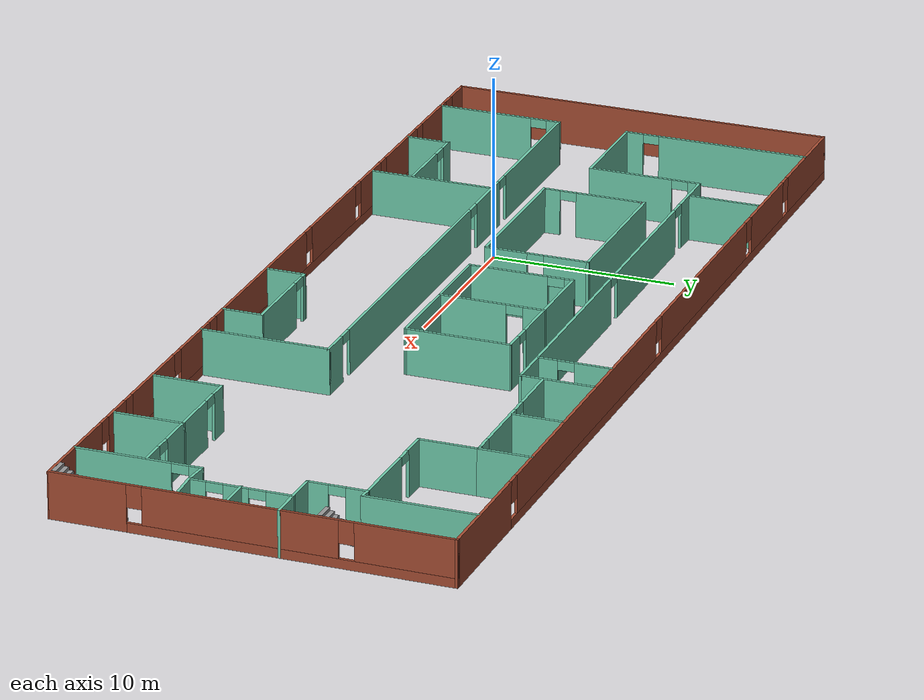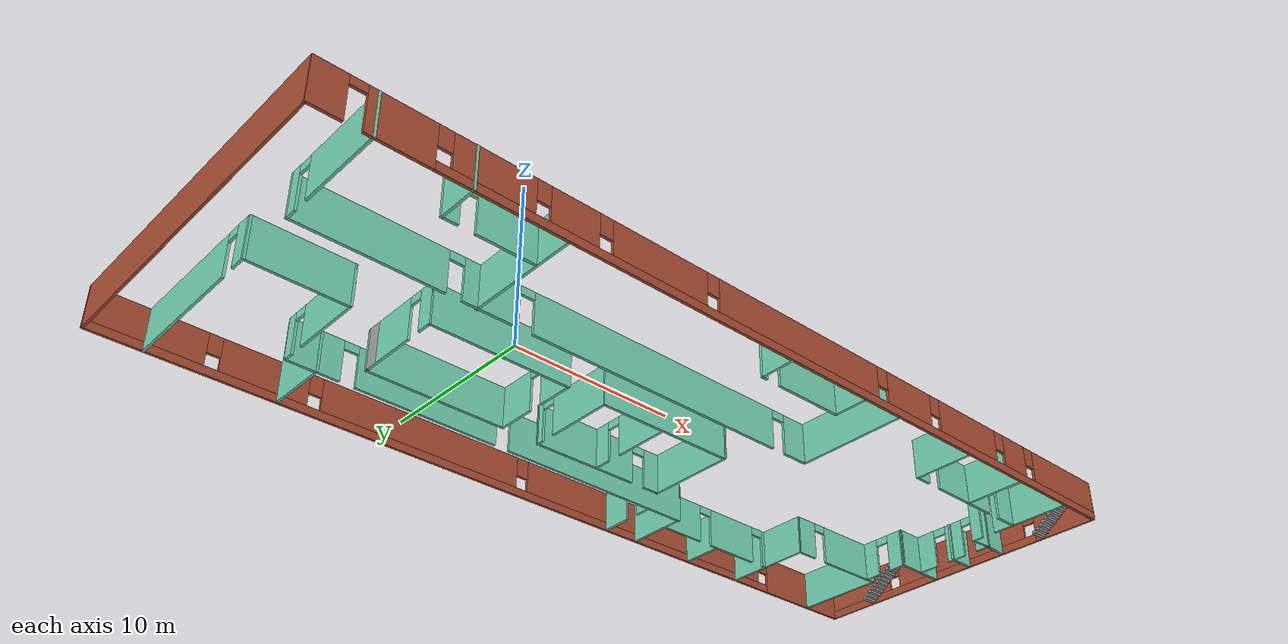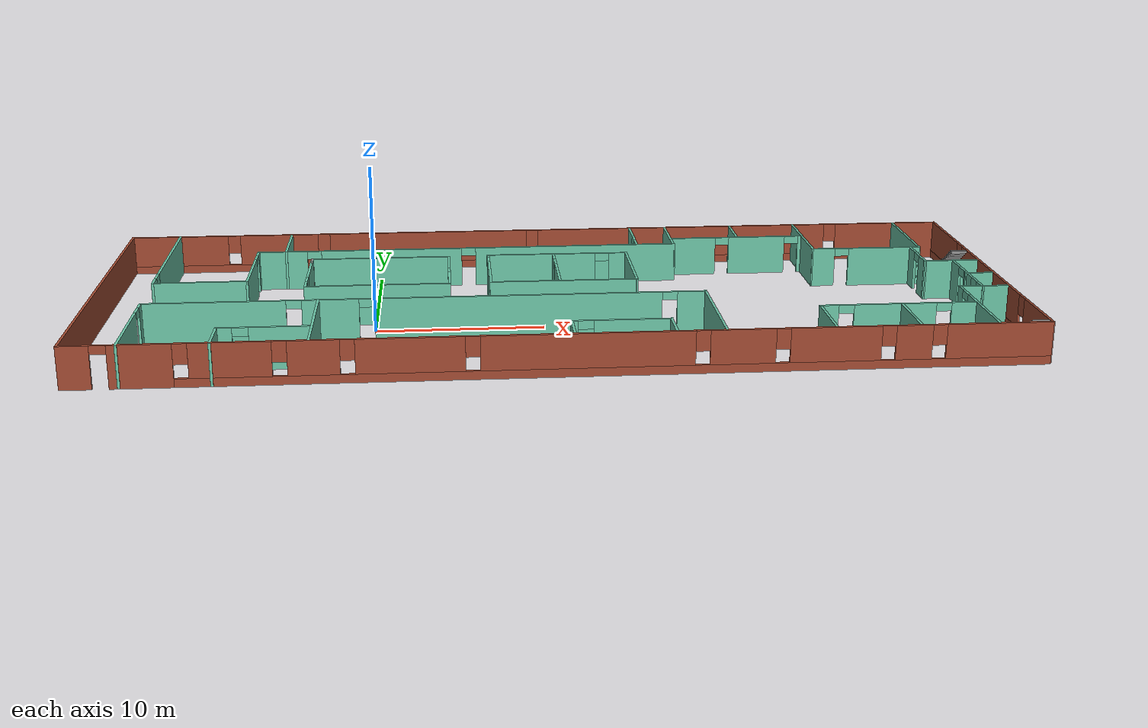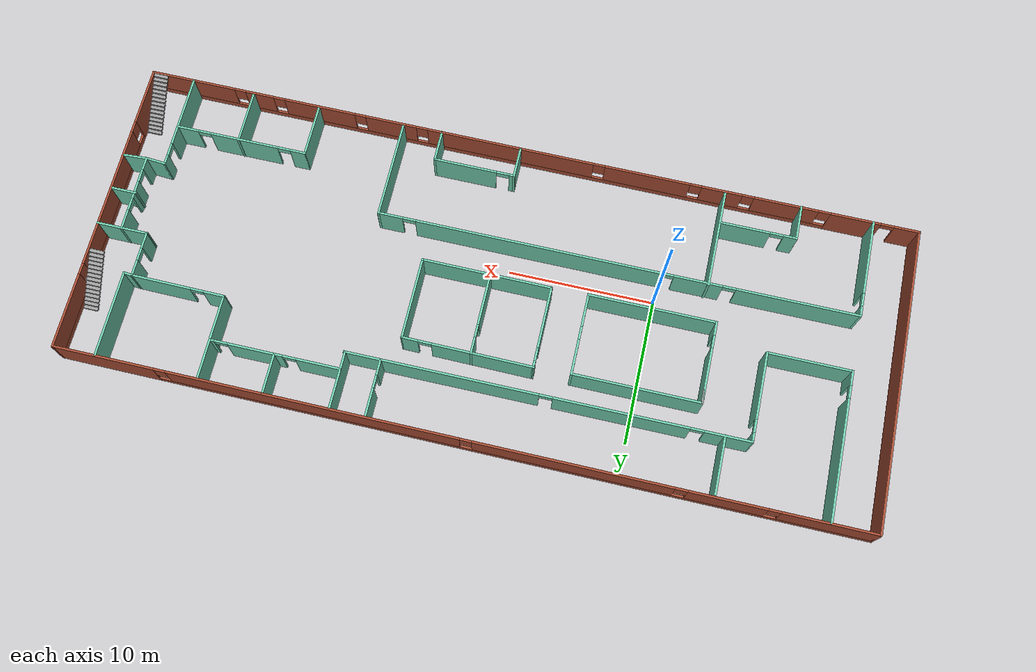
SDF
<?xml version='1.0'?>
<sdf version='1.7'>
  <model name='building'>
    <pose>10.6748 2.21075 0 0 -0 0</pose>
    <link name='Stairs_0'>
      <visual name='Stairs_0_Visual_0'>
        <pose>26.501 6.70728 0.083333 0 -0 0</pose>
        <geometry>
          <box>
            <size>1 0.233333 0.166667</size>
          </box>
        </geometry>
        <material>
          <script>
            <uri>file://media/materials/scripts/gazebo.material</uri>
            <name>Gazebo/Grey</name>
          </script>
          <ambient>0 0 0 1</ambient>
        </material>
        <meta>
          <layer>0</layer>
        </meta>
      </visual>
      <collision name='Stairs_0_Collision_0'>
        <geometry>
          <box>
            <size>1 0.233333 0.166667</size>
          </box>
        </geometry>
        <pose>26.501 6.70728 0.083333 0 -0 0</pose>
      </collision>
      <visual name='Stairs_0_Visual_1'>
        <pose>26.501 6.47394 0.25 0 -0 0</pose>
        <geometry>
          <box>
            <size>1 0.233333 0.166667</size>
          </box>
        </geometry>
        <material>
          <script>
            <uri>file://media/materials/scripts/gazebo.material</uri>
            <name>Gazebo/Grey</name>
          </script>
          <ambient>0 0 0 1</ambient>
        </material>
        <meta>
          <layer>0</layer>
        </meta>
      </visual>
      <collision name='Stairs_0_Collision_1'>
        <geometry>
          <box>
            <size>1 0.233333 0.166667</size>
          </box>
        </geometry>
        <pose>26.501 6.47394 0.25 0 -0 0</pose>
      </collision>
      <visual name='Stairs_0_Visual_2'>
        <pose>26.501 6.24061 0.416667 0 -0 0</pose>
        <geometry>
          <box>
            <size>1 0.233333 0.166667</size>
          </box>
        </geometry>
        <material>
          <script>
            <uri>file://media/materials/scripts/gazebo.material</uri>
            <name>Gazebo/Grey</name>
          </script>
          <ambient>0 0 0 1</ambient>
        </material>
        <meta>
          <layer>0</layer>
        </meta>
      </visual>
      <collision name='Stairs_0_Collision_2'>
        <geometry>
          <box>
            <size>1 0.233333 0.166667</size>
          </box>
        </geometry>
        <pose>26.501 6.24061 0.416667 0 -0 0</pose>
      </collision>
      <visual name='Stairs_0_Visual_3'>
        <pose>26.501 6.00728 0.583333 0 -0 0</pose>
        <geometry>
          <box>
            <size>1 0.233333 0.166667</size>
          </box>
        </geometry>
        <material>
          <script>
            <uri>file://media/materials/scripts/gazebo.material</uri>
            <name>Gazebo/Grey</name>
          </script>
          <ambient>0 0 0 1</ambient>
        </material>
        <meta>
          <layer>0</layer>
        </meta>
      </visual>
      <collision name='Stairs_0_Collision_3'>
        <geometry>
          <box>
            <size>1 0.233333 0.166667</size>
          </box>
        </geometry>
        <pose>26.501 6.00728 0.583333 0 -0 0</pose>
      </collision>
      <visual name='Stairs_0_Visual_4'>
        <pose>26.501 5.77394 0.75 0 -0 0</pose>
        <geometry>
          <box>
            <size>1 0.233333 0.166667</size>
          </box>
        </geometry>
        <material>
          <script>
            <uri>file://media/materials/scripts/gazebo.material</uri>
            <name>Gazebo/Grey</name>
          </script>
          <ambient>0 0 0 1</ambient>
        </material>
        <meta>
          <layer>0</layer>
        </meta>
      </visual>
      <collision name='Stairs_0_Collision_4'>
        <geometry>
          <box>
            <size>1 0.233333 0.166667</size>
          </box>
        </geometry>
        <pose>26.501 5.77394 0.75 0 -0 0</pose>
      </collision>
      <visual name='Stairs_0_Visual_5'>
        <pose>26.501 5.54061 0.916667 0 -0 0</pose>
        <geometry>
          <box>
            <size>1 0.233333 0.166667</size>
          </box>
        </geometry>
        <material>
          <script>
            <uri>file://media/materials/scripts/gazebo.material</uri>
            <name>Gazebo/Grey</name>
          </script>
          <ambient>0 0 0 1</ambient>
        </material>
        <meta>
          <layer>0</layer>
        </meta>
      </visual>
      <collision name='Stairs_0_Collision_5'>
        <geometry>
          <box>
            <size>1 0.233333 0.166667</size>
          </box>
        </geometry>
        <pose>26.501 5.54061 0.916667 0 -0 0</pose>
      </collision>
      <visual name='Stairs_0_Visual_6'>
        <pose>26.501 5.30728 1.08333 0 -0 0</pose>
        <geometry>
          <box>
            <size>1 0.233333 0.166667</size>
          </box>
        </geometry>
        <material>
          <script>
            <uri>file://media/materials/scripts/gazebo.material</uri>
            <name>Gazebo/Grey</name>
          </script>
          <ambient>0 0 0 1</ambient>
        </material>
        <meta>
          <layer>0</layer>
        </meta>
      </visual>
      <collision name='Stairs_0_Collision_6'>
        <geometry>
          <box>
            <size>1 0.233333 0.166667</size>
          </box>
        </geometry>
        <pose>26.501 5.30728 1.08333 0 -0 0</pose>
      </collision>
      <visual name='Stairs_0_Visual_7'>
        <pose>26.501 5.07395 1.25 0 -0 0</pose>
        <geometry>
          <box>
            <size>1 0.233333 0.166667</size>
          </box>
        </geometry>
        <material>
          <script>
            <uri>file://media/materials/scripts/gazebo.material</uri>
            <name>Gazebo/Grey</name>
          </script>
          <ambient>0 0 0 1</ambient>
        </material>
        <meta>
          <layer>0</layer>
        </meta>
      </visual>
      <collision name='Stairs_0_Collision_7'>
        <geometry>
          <box>
            <size>1 0.233333 0.166667</size>
          </box>
        </geometry>
        <pose>26.501 5.07395 1.25 0 -0 0</pose>
      </collision>
      <visual name='Stairs_0_Visual_8'>
        <pose>26.501 4.84061 1.41667 0 -0 0</pose>
        <geometry>
          <box>
            <size>1 0.233333 0.166667</size>
          </box>
        </geometry>
        <material>
          <script>
            <uri>file://media/materials/scripts/gazebo.material</uri>
            <name>Gazebo/Grey</name>
          </script>
          <ambient>0 0 0 1</ambient>
        </material>
        <meta>
          <layer>0</layer>
        </meta>
      </visual>
      <collision name='Stairs_0_Collision_8'>
        <geometry>
          <box>
            <size>1 0.233333 0.166667</size>
          </box>
        </geometry>
        <pose>26.501 4.84061 1.41667 0 -0 0</pose>
      </collision>
      <visual name='Stairs_0_Visual_9'>
        <pose>26.501 4.60728 1.58333 0 -0 0</pose>
        <geometry>
          <box>
            <size>1 0.233333 0.166667</size>
          </box>
        </geometry>
        <material>
          <script>
            <uri>file://media/materials/scripts/gazebo.material</uri>
            <name>Gazebo/Grey</name>
          </script>
          <ambient>0 0 0 1</ambient>
        </material>
        <meta>
          <layer>0</layer>
        </meta>
      </visual>
      <collision name='Stairs_0_Collision_9'>
        <geometry>
          <box>
            <size>1 0.233333 0.166667</size>
          </box>
        </geometry>
        <pose>26.501 4.60728 1.58333 0 -0 0</pose>
      </collision>
      <visual name='Stairs_0_Visual_10'>
        <pose>26.501 4.37394 1.75 0 -0 0</pose>
        <geometry>
          <box>
            <size>1 0.233333 0.166667</size>
          </box>
        </geometry>
        <material>
          <script>
            <uri>file://media/materials/scripts/gazebo.material</uri>
            <name>Gazebo/Grey</name>
          </script>
          <ambient>0 0 0 1</ambient>
        </material>
        <meta>
          <layer>0</layer>
        </meta>
      </visual>
      <collision name='Stairs_0_Collision_10'>
        <geometry>
          <box>
            <size>1 0.233333 0.166667</size>
          </box>
        </geometry>
        <pose>26.501 4.37394 1.75 0 -0 0</pose>
      </collision>
      <visual name='Stairs_0_Visual_11'>
        <pose>26.501 4.14061 1.91667 0 -0 0</pose>
        <geometry>
          <box>
            <size>1 0.233333 0.166667</size>
          </box>
        </geometry>
        <material>
          <script>
            <uri>file://media/materials/scripts/gazebo.material</uri>
            <name>Gazebo/Grey</name>
          </script>
          <ambient>0 0 0 1</ambient>
        </material>
        <meta>
          <layer>0</layer>
        </meta>
      </visual>
      <collision name='Stairs_0_Collision_11'>
        <geometry>
          <box>
            <size>1 0.233333 0.166667</size>
          </box>
        </geometry>
        <pose>26.501 4.14061 1.91667 0 -0 0</pose>
      </collision>
      <visual name='Stairs_0_Visual_12'>
        <pose>26.501 3.90728 2.08333 0 -0 0</pose>
        <geometry>
          <box>
            <size>1 0.233333 0.166667</size>
          </box>
        </geometry>
        <material>
          <script>
            <uri>file://media/materials/scripts/gazebo.material</uri>
            <name>Gazebo/Grey</name>
          </script>
          <ambient>0 0 0 1</ambient>
        </material>
        <meta>
          <layer>0</layer>
        </meta>
      </visual>
      <collision name='Stairs_0_Collision_12'>
        <geometry>
          <box>
            <size>1 0.233333 0.166667</size>
          </box>
        </geometry>
        <pose>26.501 3.90728 2.08333 0 -0 0</pose>
      </collision>
      <visual name='Stairs_0_Visual_13'>
        <pose>26.501 3.67394 2.25 0 -0 0</pose>
        <geometry>
          <box>
            <size>1 0.233333 0.166667</size>
          </box>
        </geometry>
        <material>
          <script>
            <uri>file://media/materials/scripts/gazebo.material</uri>
            <name>Gazebo/Grey</name>
          </script>
          <ambient>0 0 0 1</ambient>
        </material>
        <meta>
          <layer>0</layer>
        </meta>
      </visual>
      <collision name='Stairs_0_Collision_13'>
        <geometry>
          <box>
            <size>1 0.233333 0.166667</size>
          </box>
        </geometry>
        <pose>26.501 3.67394 2.25 0 -0 0</pose>
      </collision>
      <visual name='Stairs_0_Visual_14'>
        <pose>26.501 3.44061 2.41667 0 -0 0</pose>
        <geometry>
          <box>
            <size>1 0.233333 0.166667</size>
          </box>
        </geometry>
        <material>
          <script>
            <uri>file://media/materials/scripts/gazebo.material</uri>
            <name>Gazebo/Grey</name>
          </script>
          <ambient>0 0 0 1</ambient>
        </material>
        <meta>
          <layer>0</layer>
        </meta>
      </visual>
      <collision name='Stairs_0_Collision_14'>
        <geometry>
          <box>
            <size>1 0.233333 0.166667</size>
          </box>
        </geometry>
        <pose>26.501 3.44061 2.41667 0 -0 0</pose>
      </collision>
    </link>
    <link name='Stairs_1'>
      <visual name='Stairs_1_Visual_0'>
        <pose>26.4663 -7.00281 0.083333 0 -0 0</pose>
        <geometry>
          <box>
            <size>1 0.233333 0.166667</size>
          </box>
        </geometry>
        <material>
          <script>
            <uri>file://media/materials/scripts/gazebo.material</uri>
            <name>Gazebo/Grey</name>
          </script>
          <ambient>0 0 0 1</ambient>
        </material>
        <meta>
          <layer>0</layer>
        </meta>
      </visual>
      <collision name='Stairs_1_Collision_0'>
        <geometry>
          <box>
            <size>1 0.233333 0.166667</size>
          </box>
        </geometry>
        <pose>26.4663 -7.00281 0.083333 0 -0 0</pose>
      </collision>
      <visual name='Stairs_1_Visual_1'>
        <pose>26.4663 -7.23614 0.25 0 -0 0</pose>
        <geometry>
          <box>
            <size>1 0.233333 0.166667</size>
          </box>
        </geometry>
        <material>
          <script>
            <uri>file://media/materials/scripts/gazebo.material</uri>
            <name>Gazebo/Grey</name>
          </script>
          <ambient>0 0 0 1</ambient>
        </material>
        <meta>
          <layer>0</layer>
        </meta>
      </visual>
      <collision name='Stairs_1_Collision_1'>
        <geometry>
          <box>
            <size>1 0.233333 0.166667</size>
          </box>
        </geometry>
        <pose>26.4663 -7.23614 0.25 0 -0 0</pose>
      </collision>
      <visual name='Stairs_1_Visual_2'>
        <pose>26.4663 -7.46948 0.416667 0 -0 0</pose>
        <geometry>
          <box>
            <size>1 0.233333 0.166667</size>
          </box>
        </geometry>
        <material>
          <script>
            <uri>file://media/materials/scripts/gazebo.material</uri>
            <name>Gazebo/Grey</name>
          </script>
          <ambient>0 0 0 1</ambient>
        </material>
        <meta>
          <layer>0</layer>
        </meta>
      </visual>
      <collision name='Stairs_1_Collision_2'>
        <geometry>
          <box>
            <size>1 0.233333 0.166667</size>
          </box>
        </geometry>
        <pose>26.4663 -7.46948 0.416667 0 -0 0</pose>
      </collision>
      <visual name='Stairs_1_Visual_3'>
        <pose>26.4663 -7.70281 0.583333 0 -0 0</pose>
        <geometry>
          <box>
            <size>1 0.233333 0.166667</size>
          </box>
        </geometry>
        <material>
          <script>
            <uri>file://media/materials/scripts/gazebo.material</uri>
            <name>Gazebo/Grey</name>
          </script>
          <ambient>0 0 0 1</ambient>
        </material>
        <meta>
          <layer>0</layer>
        </meta>
      </visual>
      <collision name='Stairs_1_Collision_3'>
        <geometry>
          <box>
            <size>1 0.233333 0.166667</size>
          </box>
        </geometry>
        <pose>26.4663 -7.70281 0.583333 0 -0 0</pose>
      </collision>
      <visual name='Stairs_1_Visual_4'>
        <pose>26.4663 -7.93614 0.75 0 -0 0</pose>
        <geometry>
          <box>
            <size>1 0.233333 0.166667</size>
          </box>
        </geometry>
        <material>
          <script>
            <uri>file://media/materials/scripts/gazebo.material</uri>
            <name>Gazebo/Grey</name>
          </script>
          <ambient>0 0 0 1</ambient>
        </material>
        <meta>
          <layer>0</layer>
        </meta>
      </visual>
      <collision name='Stairs_1_Collision_4'>
        <geometry>
          <box>
            <size>1 0.233333 0.166667</size>
          </box>
        </geometry>
        <pose>26.4663 -7.93614 0.75 0 -0 0</pose>
      </collision>
      <visual name='Stairs_1_Visual_5'>
        <pose>26.4663 -8.16948 0.916667 0 -0 0</pose>
        <geometry>
          <box>
            <size>1 0.233333 0.166667</size>
          </box>
        </geometry>
        <material>
          <script>
            <uri>file://media/materials/scripts/gazebo.material</uri>
            <name>Gazebo/Grey</name>
          </script>
          <ambient>0 0 0 1</ambient>
        </material>
        <meta>
          <layer>0</layer>
        </meta>
      </visual>
      <collision name='Stairs_1_Collision_5'>
        <geometry>
          <box>
            <size>1 0.233333 0.166667</size>
          </box>
        </geometry>
        <pose>26.4663 -8.16948 0.916667 0 -0 0</pose>
      </collision>
      <visual name='Stairs_1_Visual_6'>
        <pose>26.4663 -8.40281 1.08333 0 -0 0</pose>
        <geometry>
          <box>
            <size>1 0.233333 0.166667</size>
          </box>
        </geometry>
        <material>
          <script>
            <uri>file://media/materials/scripts/gazebo.material</uri>
            <name>Gazebo/Grey</name>
          </script>
          <ambient>0 0 0 1</ambient>
        </material>
        <meta>
          <layer>0</layer>
        </meta>
      </visual>
      <collision name='Stairs_1_Collision_6'>
        <geometry>
          <box>
            <size>1 0.233333 0.166667</size>
          </box>
        </geometry>
        <pose>26.4663 -8.40281 1.08333 0 -0 0</pose>
      </collision>
      <visual name='Stairs_1_Visual_7'>
        <pose>26.4663 -8.63614 1.25 0 -0 0</pose>
        <geometry>
          <box>
            <size>1 0.233333 0.166667</size>
          </box>
        </geometry>
        <material>
          <script>
            <uri>file://media/materials/scripts/gazebo.material</uri>
            <name>Gazebo/Grey</name>
          </script>
          <ambient>0 0 0 1</ambient>
        </material>
        <meta>
          <layer>0</layer>
        </meta>
      </visual>
      <collision name='Stairs_1_Collision_7'>
        <geometry>
          <box>
            <size>1 0.233333 0.166667</size>
          </box>
        </geometry>
        <pose>26.4663 -8.63614 1.25 0 -0 0</pose>
      </collision>
      <visual name='Stairs_1_Visual_8'>
        <pose>26.4663 -8.86948 1.41667 0 -0 0</pose>
        <geometry>
          <box>
            <size>1 0.233333 0.166667</size>
          </box>
        </geometry>
        <material>
          <script>
            <uri>file://media/materials/scripts/gazebo.material</uri>
            <name>Gazebo/Grey</name>
          </script>
          <ambient>0 0 0 1</ambient>
        </material>
        <meta>
          <layer>0</layer>
        </meta>
      </visual>
      <collision name='Stairs_1_Collision_8'>
        <geometry>
          <box>
            <size>1 0.233333 0.166667</size>
          </box>
        </geometry>
        <pose>26.4663 -8.86948 1.41667 0 -0 0</pose>
      </collision>
      <visual name='Stairs_1_Visual_9'>
        <pose>26.4663 -9.10281 1.58333 0 -0 0</pose>
        <geometry>
          <box>
            <size>1 0.233333 0.166667</size>
          </box>
        </geometry>
        <material>
          <script>
            <uri>file://media/materials/scripts/gazebo.material</uri>
            <name>Gazebo/Grey</name>
          </script>
          <ambient>0 0 0 1</ambient>
        </material>
        <meta>
          <layer>0</layer>
        </meta>
      </visual>
      <collision name='Stairs_1_Collision_9'>
        <geometry>
          <box>
            <size>1 0.233333 0.166667</size>
          </box>
        </geometry>
        <pose>26.4663 -9.10281 1.58333 0 -0 0</pose>
      </collision>
      <visual name='Stairs_1_Visual_10'>
        <pose>26.4663 -9.33614 1.75 0 -0 0</pose>
        <geometry>
          <box>
            <size>1 0.233333 0.166667</size>
          </box>
        </geometry>
        <material>
          <script>
            <uri>file://media/materials/scripts/gazebo.material</uri>
            <name>Gazebo/Grey</name>
          </script>
          <ambient>0 0 0 1</ambient>
        </material>
        <meta>
          <layer>0</layer>
        </meta>
      </visual>
      <collision name='Stairs_1_Collision_10'>
        <geometry>
          <box>
            <size>1 0.233333 0.166667</size>
          </box>
        </geometry>
        <pose>26.4663 -9.33614 1.75 0 -0 0</pose>
      </collision>
      <visual name='Stairs_1_Visual_11'>
        <pose>26.4663 -9.56948 1.91667 0 -0 0</pose>
        <geometry>
          <box>
            <size>1 0.233333 0.166667</size>
          </box>
        </geometry>
        <material>
          <script>
            <uri>file://media/materials/scripts/gazebo.material</uri>
            <name>Gazebo/Grey</name>
          </script>
          <ambient>0 0 0 1</ambient>
        </material>
        <meta>
          <layer>0</layer>
        </meta>
      </visual>
      <collision name='Stairs_1_Collision_11'>
        <geometry>
          <box>
            <size>1 0.233333 0.166667</size>
          </box>
        </geometry>
        <pose>26.4663 -9.56948 1.91667 0 -0 0</pose>
      </collision>
      <visual name='Stairs_1_Visual_12'>
        <pose>26.4663 -9.80281 2.08333 0 -0 0</pose>
        <geometry>
          <box>
            <size>1 0.233333 0.166667</size>
          </box>
        </geometry>
        <material>
          <script>
            <uri>file://media/materials/scripts/gazebo.material</uri>
            <name>Gazebo/Grey</name>
          </script>
          <ambient>0 0 0 1</ambient>
        </material>
        <meta>
          <layer>0</layer>
        </meta>
      </visual>
      <collision name='Stairs_1_Collision_12'>
        <geometry>
          <box>
            <size>1 0.233333 0.166667</size>
          </box>
        </geometry>
        <pose>26.4663 -9.80281 2.08333 0 -0 0</pose>
      </collision>
      <visual name='Stairs_1_Visual_13'>
        <pose>26.4663 -10.0361 2.25 0 -0 0</pose>
        <geometry>
          <box>
            <size>1 0.233333 0.166667</size>
          </box>
        </geometry>
        <material>
          <script>
            <uri>file://media/materials/scripts/gazebo.material</uri>
            <name>Gazebo/Grey</name>
          </script>
          <ambient>0 0 0 1</ambient>
        </material>
        <meta>
          <layer>0</layer>
        </meta>
      </visual>
      <collision name='Stairs_1_Collision_13'>
        <geometry>
          <box>
            <size>1 0.233333 0.166667</size>
          </box>
        </geometry>
        <pose>26.4663 -10.0361 2.25 0 -0 0</pose>
      </collision>
      <visual name='Stairs_1_Visual_14'>
        <pose>26.4663 -10.2695 2.41667 0 -0 0</pose>
        <geometry>
          <box>
            <size>1 0.233333 0.166667</size>
          </box>
        </geometry>
        <material>
          <script>
            <uri>file://media/materials/scripts/gazebo.material</uri>
            <name>Gazebo/Grey</name>
          </script>
          <ambient>0 0 0 1</ambient>
        </material>
        <meta>
          <layer>0</layer>
        </meta>
      </visual>
      <collision name='Stairs_1_Collision_14'>
        <geometry>
          <box>
            <size>1 0.233333 0.166667</size>
          </box>
        </geometry>
        <pose>26.4663 -10.2695 2.41667 0 -0 0</pose>
      </collision>
    </link>
    <link name='Wall_1'>
      <collision name='Wall_1_Collision'>
        <geometry>
          <box>
            <size>20.9643 0.15 2.5</size>
          </box>
        </geometry>
        <pose>0 0 1.25 0 -0 0</pose>
      </collision>
      <visual name='Wall_1_Visual'>
        <pose>0 0 1.25 0 -0 0</pose>
        <geometry>
          <box>
            <size>20.9643 0.15 2.5</size>
          </box>
        </geometry>
        <material>
          <script>
            <uri>file://media/materials/scripts/gazebo.material</uri>
            <name>Gazebo/Bricks</name>
          </script>
          <ambient>1 1 1 1</ambient>
        </material>
        <meta>
          <layer>0</layer>
        </meta>
      </visual>
      <pose>-27.1424 0.06125 0 0 -0 -1.5708</pose>
    </link>
    <link name='Wall_17'>
      <pose>-24.0451 -6.99311 0 0 -0 1.5708</pose>
      <visual name='Wall_17_Visual_0'>
        <pose>-0.841784 0 1.25 0 -0 0</pose>
        <geometry>
          <box>
            <size>5.31643 0.15 2.5</size>
          </box>
        </geometry>
        <material>
          <script>
            <uri>file://media/materials/scripts/gazebo.material</uri>
            <name>Gazebo/Grey</name>
          </script>
          <ambient>0.435294 0.796078 0.67451 1</ambient>
        </material>
        <meta>
          <layer>0</layer>
        </meta>
      </visual>
      <collision name='Wall_17_Collision_0'>
        <geometry>
          <box>
            <size>5.31643 0.15 2.5</size>
          </box>
        </geometry>
        <pose>-0.841784 0 1.25 0 -0 0</pose>
      </collision>
      <visual name='Wall_17_Visual_1'>
        <pose>3.10822 0 1.25 0 -0 0</pose>
        <geometry>
          <box>
            <size>0.783567 0.15 2.5</size>
          </box>
        </geometry>
        <material>
          <script>
            <uri>file://media/materials/scripts/gazebo.material</uri>
            <name>Gazebo/Grey</name>
          </script>
          <ambient>0.435294 0.796078 0.67451 1</ambient>
        </material>
        <meta>
          <layer>0</layer>
        </meta>
      </visual>
      <collision name='Wall_17_Collision_1'>
        <geometry>
          <box>
            <size>0.783567 0.15 2.5</size>
          </box>
        </geometry>
        <pose>3.10822 0 1.25 0 -0 0</pose>
      </collision>
      <visual name='Wall_17_Visual_2'>
        <pose>2.26643 0 2.25 0 -0 0</pose>
        <geometry>
          <box>
            <size>0.9 0.15 0.5</size>
          </box>
        </geometry>
        <material>
          <script>
            <uri>file://media/materials/scripts/gazebo.material</uri>
            <name>Gazebo/Grey</name>
          </script>
          <ambient>0.435294 0.796078 0.67451 1</ambient>
        </material>
        <meta>
          <layer>0</layer>
        </meta>
      </visual>
      <collision name='Wall_17_Collision_2'>
        <geometry>
          <box>
            <size>0.9 0.15 0.5</size>
          </box>
        </geometry>
        <pose>2.26643 0 2.25 0 -0 0</pose>
      </collision>
    </link>
    <link name='Wall_19'>
      <pose>-24.0451 5.37983 0 0 -0 1.5708</pose>
      <visual name='Wall_19_Visual_0'>
        <pose>-4.60412 0 1.25 0 -0 0</pose>
        <geometry>
          <box>
            <size>1.04177 0.15 2.5</size>
          </box>
        </geometry>
        <material>
          <script>
            <uri>file://media/materials/scripts/gazebo.material</uri>
            <name>Gazebo/Grey</name>
          </script>
          <ambient>0.435294 0.796078 0.67451 1</ambient>
        </material>
        <meta>
          <layer>0</layer>
        </meta>
      </visual>
      <collision name='Wall_19_Collision_0'>
        <geometry>
          <box>
            <size>1.04177 0.15 2.5</size>
          </box>
        </geometry>
        <pose>-4.60412 0 1.25 0 -0 0</pose>
      </collision>
      <visual name='Wall_19_Visual_1'>
        <pose>0.970883 0 1.25 0 -0 0</pose>
        <geometry>
          <box>
            <size>8.30823 0.15 2.5</size>
          </box>
        </geometry>
        <material>
          <script>
            <uri>file://media/materials/scripts/gazebo.material</uri>
            <name>Gazebo/Grey</name>
          </script>
          <ambient>0.435294 0.796078 0.67451 1</ambient>
        </material>
        <meta>
          <layer>0</layer>
        </meta>
      </visual>
      <collision name='Wall_19_Collision_1'>
        <geometry>
          <box>
            <size>8.30823 0.15 2.5</size>
          </box>
        </geometry>
        <pose>0.970883 0 1.25 0 -0 0</pose>
      </collision>
      <visual name='Wall_19_Visual_2'>
        <pose>-3.63323 0 2.25 0 -0 0</pose>
        <geometry>
          <box>
            <size>0.9 0.15 0.5</size>
          </box>
        </geometry>
        <material>
          <script>
            <uri>file://media/materials/scripts/gazebo.material</uri>
            <name>Gazebo/Grey</name>
          </script>
          <ambient>0.435294 0.796078 0.67451 1</ambient>
        </material>
        <meta>
          <layer>0</layer>
        </meta>
      </visual>
      <collision name='Wall_19_Collision_2'>
        <geometry>
          <box>
            <size>0.9 0.15 0.5</size>
          </box>
        </geometry>
        <pose>-3.63323 0 2.25 0 -0 0</pose>
      </collision>
    </link>
    <link name='Wall_2'>
      <pose>-0.030827 -10.4379 0 0 -0 -0.001122</pose>
      <visual name='Wall_2_Visual_0'>
        <pose>-26.3076 0 1.25 0 -0 0</pose>
        <geometry>
          <box>
            <size>1.75806 0.15 2.5</size>
          </box>
        </geometry>
        <material>
          <script>
            <uri>file://media/materials/scripts/gazebo.material</uri>
            <name>Gazebo/Bricks</name>
          </script>
          <ambient>1 1 1 1</ambient>
        </material>
        <meta>
          <layer>0</layer>
        </meta>
      </visual>
      <collision name='Wall_2_Collision_0'>
        <geometry>
          <box>
            <size>1.75806 0.15 2.5</size>
          </box>
        </geometry>
        <pose>-26.3076 0 1.25 0 -0 0</pose>
      </collision>
      <visual name='Wall_2_Visual_1'>
        <pose>-22.8085 0 1.25 0 -0 0</pose>
        <geometry>
          <box>
            <size>3.44002 0.15 2.5</size>
          </box>
        </geometry>
        <material>
          <script>
            <uri>file://media/materials/scripts/gazebo.material</uri>
            <name>Gazebo/Bricks</name>
          </script>
          <ambient>1 1 1 1</ambient>
        </material>
        <meta>
          <layer>0</layer>
        </meta>
      </visual>
      <collision name='Wall_2_Collision_1'>
        <geometry>
          <box>
            <size>3.44002 0.15 2.5</size>
          </box>
        </geometry>
        <pose>-22.8085 0 1.25 0 -0 0</pose>
      </collision>
      <visual name='Wall_2_Visual_2'>
        <pose>3.04904 0 0.25 0 -0 0</pose>
        <geometry>
          <box>
            <size>48.2751 0.15 0.5</size>
          </box>
        </geometry>
        <material>
          <script>
            <uri>file://media/materials/scripts/gazebo.material</uri>
            <name>Gazebo/Bricks</name>
          </script>
          <ambient>1 1 1 1</ambient>
        </material>
        <meta>
          <layer>0</layer>
        </meta>
      </visual>
      <collision name='Wall_2_Collision_2'>
        <geometry>
          <box>
            <size>48.2751 0.15 0.5</size>
          </box>
        </geometry>
        <pose>3.04904 0 0.25 0 -0 0</pose>
      </collision>
      <visual name='Wall_2_Visual_3'>
        <pose>-18.0663 0 1.5 0 -0 0</pose>
        <geometry>
          <box>
            <size>4.44444 0.15 2</size>
          </box>
        </geometry>
        <material>
          <script>
            <uri>file://media/materials/scripts/gazebo.material</uri>
            <name>Gazebo/Bricks</name>
          </script>
          <ambient>1 1 1 1</ambient>
        </material>
        <meta>
          <layer>0</layer>
        </meta>
      </visual>
      <collision name='Wall_2_Collision_3'>
        <geometry>
          <box>
            <size>4.44444 0.15 2</size>
          </box>
        </geometry>
        <pose>-18.0663 0 1.5 0 -0 0</pose>
      </collision>
      <visual name='Wall_2_Visual_4'>
        <pose>-13.6333 0 1.5 0 -0 0</pose>
        <geometry>
          <box>
            <size>2.8216 0.15 2</size>
          </box>
        </geometry>
        <material>
          <script>
            <uri>file://media/materials/scripts/gazebo.material</uri>
            <name>Gazebo/Bricks</name>
          </script>
          <ambient>1 1 1 1</ambient>
        </material>
        <meta>
          <layer>0</layer>
        </meta>
      </visual>
      <collision name='Wall_2_Collision_4'>
        <geometry>
          <box>
            <size>2.8216 0.15 2</size>
          </box>
        </geometry>
        <pose>-13.6333 0 1.5 0 -0 0</pose>
      </collision>
      <visual name='Wall_2_Visual_5'>
        <pose>-8.44766 0 1.5 0 -0 0</pose>
        <geometry>
          <box>
            <size>5.94963 0.15 2</size>
          </box>
        </geometry>
        <material>
          <script>
            <uri>file://media/materials/scripts/gazebo.material</uri>
            <name>Gazebo/Bricks</name>
          </script>
          <ambient>1 1 1 1</ambient>
        </material>
        <meta>
          <layer>0</layer>
        </meta>
      </visual>
      <collision name='Wall_2_Collision_5'>
        <geometry>
          <box>
            <size>5.94963 0.15 2</size>
          </box>
        </geometry>
        <pose>-8.44766 0 1.5 0 -0 0</pose>
      </collision>
      <visual name='Wall_2_Visual_6'>
        <pose>1.21919 0 1.5 0 -0 0</pose>
        <geometry>
          <box>
            <size>11.7841 0.15 2</size>
          </box>
        </geometry>
        <material>
          <script>
            <uri>file://media/materials/scripts/gazebo.material</uri>
            <name>Gazebo/Bricks</name>
          </script>
          <ambient>1 1 1 1</ambient>
        </material>
        <meta>
          <layer>0</layer>
        </meta>
      </visual>
      <collision name='Wall_2_Collision_6'>
        <geometry>
          <box>
            <size>11.7841 0.15 2</size>
          </box>
        </geometry>
        <pose>1.21919 0 1.5 0 -0 0</pose>
      </collision>
      <visual name='Wall_2_Visual_7'>
        <pose>9.73615 0 1.5 0 -0 0</pose>
        <geometry>
          <box>
            <size>3.64987 0.15 2</size>
          </box>
        </geometry>
        <material>
          <script>
            <uri>file://media/materials/scripts/gazebo.material</uri>
            <name>Gazebo/Bricks</name>
          </script>
          <ambient>1 1 1 1</ambient>
        </material>
        <meta>
          <layer>0</layer>
        </meta>
      </visual>
      <collision name='Wall_2_Collision_7'>
        <geometry>
          <box>
            <size>3.64987 0.15 2</size>
          </box>
        </geometry>
        <pose>9.73615 0 1.5 0 -0 0</pose>
      </collision>
      <visual name='Wall_2_Visual_8'>
        <pose>14.9144 0 1.5 0 -0 0</pose>
        <geometry>
          <box>
            <size>5.10667 0.15 2</size>
          </box>
        </geometry>
        <material>
          <script>
            <uri>file://media/materials/scripts/gazebo.material</uri>
            <name>Gazebo/Bricks</name>
          </script>
          <ambient>1 1 1 1</ambient>
        </material>
        <meta>
          <layer>0</layer>
        </meta>
      </visual>
      <collision name='Wall_2_Collision_8'>
        <geometry>
          <box>
            <size>5.10667 0.15 2</size>
          </box>
        </geometry>
        <pose>14.9144 0 1.5 0 -0 0</pose>
      </collision>
      <visual name='Wall_2_Visual_9'>
        <pose>19.2961 0 1.5 0 -0 0</pose>
        <geometry>
          <box>
            <size>2.05672 0.15 2</size>
          </box>
        </geometry>
        <material>
          <script>
            <uri>file://media/materials/scripts/gazebo.material</uri>
            <name>Gazebo/Bricks</name>
          </script>
          <ambient>1 1 1 1</ambient>
        </material>
        <meta>
          <layer>0</layer>
        </meta>
      </visual>
      <collision name='Wall_2_Collision_9'>
        <geometry>
          <box>
            <size>2.05672 0.15 2</size>
          </box>
        </geometry>
        <pose>19.2961 0 1.5 0 -0 0</pose>
      </collision>
      <visual name='Wall_2_Visual_10'>
        <pose>24.1555 0 1.5 0 -0 0</pose>
        <geometry>
          <box>
            <size>6.06212 0.15 2</size>
          </box>
        </geometry>
        <material>
          <script>
            <uri>file://media/materials/scripts/gazebo.material</uri>
            <name>Gazebo/Bricks</name>
          </script>
          <ambient>1 1 1 1</ambient>
        </material>
        <meta>
          <layer>0</layer>
        </meta>
      </visual>
      <collision name='Wall_2_Collision_10'>
        <geometry>
          <box>
            <size>6.06212 0.15 2</size>
          </box>
        </geometry>
        <pose>24.1555 0 1.5 0 -0 0</pose>
      </collision>
      <visual name='Wall_2_Visual_11'>
        <pose>-20.6885 0 1.9 0 -0 0</pose>
        <geometry>
          <box>
            <size>0.8 0.15 1.2</size>
          </box>
        </geometry>
        <material>
          <script>
            <uri>file://media/materials/scripts/gazebo.material</uri>
            <name>Gazebo/Bricks</name>
          </script>
          <ambient>1 1 1 1</ambient>
        </material>
        <meta>
          <layer>0</layer>
        </meta>
      </visual>
      <collision name='Wall_2_Collision_11'>
        <geometry>
          <box>
            <size>0.8 0.15 1.2</size>
          </box>
        </geometry>
        <pose>-20.6885 0 1.9 0 -0 0</pose>
      </collision>
      <visual name='Wall_2_Visual_12'>
        <pose>-15.4441 0 1.9 0 -0 0</pose>
        <geometry>
          <box>
            <size>0.8 0.15 1.2</size>
          </box>
        </geometry>
        <material>
          <script>
            <uri>file://media/materials/scripts/gazebo.material</uri>
            <name>Gazebo/Bricks</name>
          </script>
          <ambient>1 1 1 1</ambient>
        </material>
        <meta>
          <layer>0</layer>
        </meta>
      </visual>
      <collision name='Wall_2_Collision_12'>
        <geometry>
          <box>
            <size>0.8 0.15 1.2</size>
          </box>
        </geometry>
        <pose>-15.4441 0 1.9 0 -0 0</pose>
      </collision>
      <visual name='Wall_2_Visual_13'>
        <pose>-11.8225 0 1.9 0 -0 0</pose>
        <geometry>
          <box>
            <size>0.8 0.15 1.2</size>
          </box>
        </geometry>
        <material>
          <script>
            <uri>file://media/materials/scripts/gazebo.material</uri>
            <name>Gazebo/Bricks</name>
          </script>
          <ambient>1 1 1 1</ambient>
        </material>
        <meta>
          <layer>0</layer>
        </meta>
      </visual>
      <collision name='Wall_2_Collision_13'>
        <geometry>
          <box>
            <size>0.8 0.15 1.2</size>
          </box>
        </geometry>
        <pose>-11.8225 0 1.9 0 -0 0</pose>
      </collision>
      <visual name='Wall_2_Visual_14'>
        <pose>-5.07284 0 1.9 0 -0 0</pose>
        <geometry>
          <box>
            <size>0.8 0.15 1.2</size>
          </box>
        </geometry>
        <material>
          <script>
            <uri>file://media/materials/scripts/gazebo.material</uri>
            <name>Gazebo/Bricks</name>
          </script>
          <ambient>1 1 1 1</ambient>
        </material>
        <meta>
          <layer>0</layer>
        </meta>
      </visual>
      <collision name='Wall_2_Collision_14'>
        <geometry>
          <box>
            <size>0.8 0.15 1.2</size>
          </box>
        </geometry>
        <pose>-5.07284 0 1.9 0 -0 0</pose>
      </collision>
      <visual name='Wall_2_Visual_15'>
        <pose>7.51122 0 1.9 0 -0 0</pose>
        <geometry>
          <box>
            <size>0.8 0.15 1.2</size>
          </box>
        </geometry>
        <material>
          <script>
            <uri>file://media/materials/scripts/gazebo.material</uri>
            <name>Gazebo/Bricks</name>
          </script>
          <ambient>1 1 1 1</ambient>
        </material>
        <meta>
          <layer>0</layer>
        </meta>
      </visual>
      <collision name='Wall_2_Collision_15'>
        <geometry>
          <box>
            <size>0.8 0.15 1.2</size>
          </box>
        </geometry>
        <pose>7.51122 0 1.9 0 -0 0</pose>
      </collision>
      <visual name='Wall_2_Visual_16'>
        <pose>11.9611 0 1.9 0 -0 0</pose>
        <geometry>
          <box>
            <size>0.8 0.15 1.2</size>
          </box>
        </geometry>
        <material>
          <script>
            <uri>file://media/materials/scripts/gazebo.material</uri>
            <name>Gazebo/Bricks</name>
          </script>
          <ambient>1 1 1 1</ambient>
        </material>
        <meta>
          <layer>0</layer>
        </meta>
      </visual>
      <collision name='Wall_2_Collision_16'>
        <geometry>
          <box>
            <size>0.8 0.15 1.2</size>
          </box>
        </geometry>
        <pose>11.9611 0 1.9 0 -0 0</pose>
      </collision>
      <visual name='Wall_2_Visual_17'>
        <pose>17.8678 0 1.9 0 -0 0</pose>
        <geometry>
          <box>
            <size>0.8 0.15 1.2</size>
          </box>
        </geometry>
        <material>
          <script>
            <uri>file://media/materials/scripts/gazebo.material</uri>
            <name>Gazebo/Bricks</name>
          </script>
          <ambient>1 1 1 1</ambient>
        </material>
        <meta>
          <layer>0</layer>
        </meta>
      </visual>
      <collision name='Wall_2_Collision_17'>
        <geometry>
          <box>
            <size>0.8 0.15 1.2</size>
          </box>
        </geometry>
        <pose>17.8678 0 1.9 0 -0 0</pose>
      </collision>
      <visual name='Wall_2_Visual_18'>
        <pose>20.7245 0 1.9 0 -0 0</pose>
        <geometry>
          <box>
            <size>0.8 0.15 1.2</size>
          </box>
        </geometry>
        <material>
          <script>
            <uri>file://media/materials/scripts/gazebo.material</uri>
            <name>Gazebo/Bricks</name>
          </script>
          <ambient>1 1 1 1</ambient>
        </material>
        <meta>
          <layer>0</layer>
        </meta>
      </visual>
      <collision name='Wall_2_Collision_18'>
        <geometry>
          <box>
            <size>0.8 0.15 1.2</size>
          </box>
        </geometry>
        <pose>20.7245 0 1.9 0 -0 0</pose>
      </collision>
      <visual name='Wall_2_Visual_19'>
        <pose>-24.9785 0 2.25 0 -0 0</pose>
        <geometry>
          <box>
            <size>0.9 0.15 0.5</size>
          </box>
        </geometry>
        <material>
          <script>
            <uri>file://media/materials/scripts/gazebo.material</uri>
            <name>Gazebo/Bricks</name>
          </script>
          <ambient>1 1 1 1</ambient>
        </material>
        <meta>
          <layer>0</layer>
        </meta>
      </visual>
      <collision name='Wall_2_Collision_19'>
        <geometry>
          <box>
            <size>0.9 0.15 0.5</size>
          </box>
        </geometry>
        <pose>-24.9785 0 2.25 0 -0 0</pose>
      </collision>
    </link>
    <link name='Wall_22'>
      <pose>-7.62009 -3.56811 0 0 -0 0</pose>
      <visual name='Wall_22_Visual_0'>
        <pose>-12.3198 0 1.25 0 -0 0</pose>
        <geometry>
          <box>
            <size>8.36047 0.15 2.5</size>
          </box>
        </geometry>
        <material>
          <script>
            <uri>file://media/materials/scripts/gazebo.material</uri>
            <name>Gazebo/Grey</name>
          </script>
          <ambient>0.435294 0.796078 0.67451 1</ambient>
        </material>
        <meta>
          <layer>0</layer>
        </meta>
      </visual>
      <collision name='Wall_22_Collision_0'>
        <geometry>
          <box>
            <size>8.36047 0.15 2.5</size>
          </box>
        </geometry>
        <pose>-12.3198 0 1.25 0 -0 0</pose>
      </collision>
      <visual name='Wall_22_Visual_1'>
        <pose>-5.58622 0 1.25 0 -0 0</pose>
        <geometry>
          <box>
            <size>3.3066 0.15 2.5</size>
          </box>
        </geometry>
        <material>
          <script>
            <uri>file://media/materials/scripts/gazebo.material</uri>
            <name>Gazebo/Grey</name>
          </script>
          <ambient>0.435294 0.796078 0.67451 1</ambient>
        </material>
        <meta>
          <layer>0</layer>
        </meta>
      </visual>
      <collision name='Wall_22_Collision_1'>
        <geometry>
          <box>
            <size>3.3066 0.15 2.5</size>
          </box>
        </geometry>
        <pose>-5.58622 0 1.25 0 -0 0</pose>
      </collision>
      <visual name='Wall_22_Visual_2'>
        <pose>5.40154 0 1.25 0 -0 0</pose>
        <geometry>
          <box>
            <size>16.8689 0.15 2.5</size>
          </box>
        </geometry>
        <material>
          <script>
            <uri>file://media/materials/scripts/gazebo.material</uri>
            <name>Gazebo/Grey</name>
          </script>
          <ambient>0.435294 0.796078 0.67451 1</ambient>
        </material>
        <meta>
          <layer>0</layer>
        </meta>
      </visual>
      <collision name='Wall_22_Collision_2'>
        <geometry>
          <box>
            <size>16.8689 0.15 2.5</size>
          </box>
        </geometry>
        <pose>5.40154 0 1.25 0 -0 0</pose>
      </collision>
      <visual name='Wall_22_Visual_3'>
        <pose>15.618 0 1.25 0 -0 0</pose>
        <geometry>
          <box>
            <size>1.76399 0.15 2.5</size>
          </box>
        </geometry>
        <material>
          <script>
            <uri>file://media/materials/scripts/gazebo.material</uri>
            <name>Gazebo/Grey</name>
          </script>
          <ambient>0.435294 0.796078 0.67451 1</ambient>
        </material>
        <meta>
          <layer>0</layer>
        </meta>
      </visual>
      <collision name='Wall_22_Collision_3'>
        <geometry>
          <box>
            <size>1.76399 0.15 2.5</size>
          </box>
        </geometry>
        <pose>15.618 0 1.25 0 -0 0</pose>
      </collision>
      <visual name='Wall_22_Visual_4'>
        <pose>-7.68952 0 2.25 0 -0 0</pose>
        <geometry>
          <box>
            <size>0.9 0.15 0.5</size>
          </box>
        </geometry>
        <material>
          <script>
            <uri>file://media/materials/scripts/gazebo.material</uri>
            <name>Gazebo/Grey</name>
          </script>
          <ambient>0.435294 0.796078 0.67451 1</ambient>
        </material>
        <meta>
          <layer>0</layer>
        </meta>
      </visual>
      <collision name='Wall_22_Collision_4'>
        <geometry>
          <box>
            <size>0.9 0.15 0.5</size>
          </box>
        </geometry>
        <pose>-7.68952 0 2.25 0 -0 0</pose>
      </collision>
      <visual name='Wall_22_Visual_5'>
        <pose>-3.48292 0 2.25 0 -0 0</pose>
        <geometry>
          <box>
            <size>0.9 0.15 0.5</size>
          </box>
        </geometry>
        <material>
          <script>
            <uri>file://media/materials/scripts/gazebo.material</uri>
            <name>Gazebo/Grey</name>
          </script>
          <ambient>0.435294 0.796078 0.67451 1</ambient>
        </material>
        <meta>
          <layer>0</layer>
        </meta>
      </visual>
      <collision name='Wall_22_Collision_5'>
        <geometry>
          <box>
            <size>0.9 0.15 0.5</size>
          </box>
        </geometry>
        <pose>-3.48292 0 2.25 0 -0 0</pose>
      </collision>
      <visual name='Wall_22_Visual_6'>
        <pose>14.286 0 2.25 0 -0 0</pose>
        <geometry>
          <box>
            <size>0.9 0.15 0.5</size>
          </box>
        </geometry>
        <material>
          <script>
            <uri>file://media/materials/scripts/gazebo.material</uri>
            <name>Gazebo/Grey</name>
          </script>
          <ambient>0.435294 0.796078 0.67451 1</ambient>
        </material>
        <meta>
          <layer>0</layer>
        </meta>
      </visual>
      <collision name='Wall_22_Collision_6'>
        <geometry>
          <box>
            <size>0.9 0.15 0.5</size>
          </box>
        </geometry>
        <pose>14.286 0 2.25 0 -0 0</pose>
      </collision>
    </link>
    <link name='Wall_23'>
      <collision name='Wall_23_Collision'>
        <geometry>
          <box>
            <size>7 0.15 2.5</size>
          </box>
        </geometry>
        <pose>0 0 1.25 0 -0 0</pose>
      </collision>
      <visual name='Wall_23_Visual'>
        <pose>0 0 1.25 0 -0 0</pose>
        <geometry>
          <box>
            <size>7 0.15 2.5</size>
          </box>
        </geometry>
        <material>
          <script>
            <uri>file://media/materials/scripts/gazebo.material</uri>
            <name>Gazebo/Grey</name>
          </script>
          <ambient>0.435294 0.796078 0.67451 1</ambient>
        </material>
        <meta>
          <layer>0</layer>
        </meta>
      </visual>
      <pose>8.80491 -6.99311 0 0 -0 -1.5708</pose>
    </link>
    <link name='Wall_25'>
      <collision name='Wall_25_Collision'>
        <geometry>
          <box>
            <size>7 0.15 2.5</size>
          </box>
        </geometry>
        <pose>0 0 1.25 0 -0 0</pose>
      </collision>
      <visual name='Wall_25_Visual'>
        <pose>0 0 1.25 0 -0 0</pose>
        <geometry>
          <box>
            <size>7 0.15 2.5</size>
          </box>
        </geometry>
        <material>
          <script>
            <uri>file://media/materials/scripts/gazebo.material</uri>
            <name>Gazebo/Grey</name>
          </script>
          <ambient>0.435294 0.796078 0.67451 1</ambient>
        </material>
        <meta>
          <layer>0</layer>
        </meta>
      </visual>
      <pose>-13.9058 -6.92493 0 0 -0 -1.5708</pose>
    </link>
    <link name='Wall_27'>
      <collision name='Wall_27_Collision'>
        <geometry>
          <box>
            <size>5.75 0.15 2.5</size>
          </box>
        </geometry>
        <pose>0 0 1.25 0 -0 0</pose>
      </collision>
      <visual name='Wall_27_Visual'>
        <pose>0 0 1.25 0 -0 0</pose>
        <geometry>
          <box>
            <size>5.75 0.15 2.5</size>
          </box>
        </geometry>
        <material>
          <script>
            <uri>file://media/materials/scripts/gazebo.material</uri>
            <name>Gazebo/Grey</name>
          </script>
          <ambient>0.435294 0.796078 0.67451 1</ambient>
        </material>
        <meta>
          <layer>0</layer>
        </meta>
      </visual>
      <pose>-21.2451 0.32983 0 0 -0 0</pose>
    </link>
    <link name='Wall_28'>
      <pose>-18.4451 3.37983 0 0 -0 1.5708</pose>
      <visual name='Wall_28_Visual_0'>
        <pose>-0.805712 0 1.25 0 -0 0</pose>
        <geometry>
          <box>
            <size>4.63858 0.15 2.5</size>
          </box>
        </geometry>
        <material>
          <script>
            <uri>file://media/materials/scripts/gazebo.material</uri>
            <name>Gazebo/Grey</name>
          </script>
          <ambient>0.435294 0.796078 0.67451 1</ambient>
        </material>
        <meta>
          <layer>0</layer>
        </meta>
      </visual>
      <collision name='Wall_28_Collision_0'>
        <geometry>
          <box>
            <size>4.63858 0.15 2.5</size>
          </box>
        </geometry>
        <pose>-0.805712 0 1.25 0 -0 0</pose>
      </collision>
      <visual name='Wall_28_Visual_1'>
        <pose>2.76929 0 1.25 0 -0 0</pose>
        <geometry>
          <box>
            <size>0.711425 0.15 2.5</size>
          </box>
        </geometry>
        <material>
          <script>
            <uri>file://media/materials/scripts/gazebo.material</uri>
            <name>Gazebo/Grey</name>
          </script>
          <ambient>0.435294 0.796078 0.67451 1</ambient>
        </material>
        <meta>
          <layer>0</layer>
        </meta>
      </visual>
      <collision name='Wall_28_Collision_1'>
        <geometry>
          <box>
            <size>0.711425 0.15 2.5</size>
          </box>
        </geometry>
        <pose>2.76929 0 1.25 0 -0 0</pose>
      </collision>
      <visual name='Wall_28_Visual_2'>
        <pose>1.96358 0 2.25 0 -0 0</pose>
        <geometry>
          <box>
            <size>0.9 0.15 0.5</size>
          </box>
        </geometry>
        <material>
          <script>
            <uri>file://media/materials/scripts/gazebo.material</uri>
            <name>Gazebo/Grey</name>
          </script>
          <ambient>0.435294 0.796078 0.67451 1</ambient>
        </material>
        <meta>
          <layer>0</layer>
        </meta>
      </visual>
      <collision name='Wall_28_Collision_2'>
        <geometry>
          <box>
            <size>0.9 0.15 0.5</size>
          </box>
        </geometry>
        <pose>1.96358 0 2.25 0 -0 0</pose>
      </collision>
    </link>
    <link name='Wall_29'>
      <pose>-4.99334 6.45658 0 0 -0 0.001989</pose>
      <visual name='Wall_29_Visual_0'>
        <pose>-11.9411 0 1.25 0 -0 0</pose>
        <geometry>
          <box>
            <size>3.17132 0.15 2.5</size>
          </box>
        </geometry>
        <material>
          <script>
            <uri>file://media/materials/scripts/gazebo.material</uri>
            <name>Gazebo/Grey</name>
          </script>
          <ambient>0.435294 0.796078 0.67451 1</ambient>
        </material>
        <meta>
          <layer>0</layer>
        </meta>
      </visual>
      <collision name='Wall_29_Collision_0'>
        <geometry>
          <box>
            <size>3.17132 0.15 2.5</size>
          </box>
        </geometry>
        <pose>-11.9411 0 1.25 0 -0 0</pose>
      </collision>
      <visual name='Wall_29_Visual_1'>
        <pose>-4.94991 0 1.25 0 -0 0</pose>
        <geometry>
          <box>
            <size>9.01109 0.15 2.5</size>
          </box>
        </geometry>
        <material>
          <script>
            <uri>file://media/materials/scripts/gazebo.material</uri>
            <name>Gazebo/Grey</name>
          </script>
          <ambient>0.435294 0.796078 0.67451 1</ambient>
        </material>
        <meta>
          <layer>0</layer>
        </meta>
      </visual>
      <collision name='Wall_29_Collision_1'>
        <geometry>
          <box>
            <size>9.01109 0.15 2.5</size>
          </box>
        </geometry>
        <pose>-4.94991 0 1.25 0 -0 0</pose>
      </collision>
      <visual name='Wall_29_Visual_2'>
        <pose>6.99121 0 1.25 0 -0 0</pose>
        <geometry>
          <box>
            <size>13.0711 0.15 2.5</size>
          </box>
        </geometry>
        <material>
          <script>
            <uri>file://media/materials/scripts/gazebo.material</uri>
            <name>Gazebo/Grey</name>
          </script>
          <ambient>0.435294 0.796078 0.67451 1</ambient>
        </material>
        <meta>
          <layer>0</layer>
        </meta>
      </visual>
      <collision name='Wall_29_Collision_2'>
        <geometry>
          <box>
            <size>13.0711 0.15 2.5</size>
          </box>
        </geometry>
        <pose>6.99121 0 1.25 0 -0 0</pose>
      </collision>
      <visual name='Wall_29_Visual_3'>
        <pose>-9.90545 0 2.25 0 -0 0</pose>
        <geometry>
          <box>
            <size>0.9 0.15 0.5</size>
          </box>
        </geometry>
        <material>
          <script>
            <uri>file://media/materials/scripts/gazebo.material</uri>
            <name>Gazebo/Grey</name>
          </script>
          <ambient>0.435294 0.796078 0.67451 1</ambient>
        </material>
        <meta>
          <layer>0</layer>
        </meta>
      </visual>
      <collision name='Wall_29_Collision_3'>
        <geometry>
          <box>
            <size>0.9 0.15 0.5</size>
          </box>
        </geometry>
        <pose>-9.90545 0 2.25 0 -0 0</pose>
      </collision>
      <visual name='Wall_29_Visual_4'>
        <pose>0.005638 0 2.25 0 -0 0</pose>
        <geometry>
          <box>
            <size>0.9 0.15 0.5</size>
          </box>
        </geometry>
        <material>
          <script>
            <uri>file://media/materials/scripts/gazebo.material</uri>
            <name>Gazebo/Grey</name>
          </script>
          <ambient>0.435294 0.796078 0.67451 1</ambient>
        </material>
        <meta>
          <layer>0</layer>
        </meta>
      </visual>
      <collision name='Wall_29_Collision_4'>
        <geometry>
          <box>
            <size>0.9 0.15 0.5</size>
          </box>
        </geometry>
        <pose>0.005638 0 2.25 0 -0 0</pose>
      </collision>
    </link>
    <link name='Wall_3'>
      <pose>27.1115 -0.030347 0 0 -0 1.56785</pose>
      <visual name='Wall_3_Visual_0'>
        <pose>-8.45604 0 1.25 0 -0 0</pose>
        <geometry>
          <box>
            <size>4.11386 0.15 2.5</size>
          </box>
        </geometry>
        <material>
          <script>
            <uri>file://media/materials/scripts/gazebo.material</uri>
            <name>Gazebo/Bricks</name>
          </script>
          <ambient>1 1 1 1</ambient>
        </material>
        <meta>
          <layer>0</layer>
        </meta>
      </visual>
      <collision name='Wall_3_Collision_0'>
        <geometry>
          <box>
            <size>4.11386 0.15 2.5</size>
          </box>
        </geometry>
        <pose>-8.45604 0 1.25 0 -0 0</pose>
      </collision>
      <visual name='Wall_3_Visual_1'>
        <pose>2.05693 0 0.25 0 -0 0</pose>
        <geometry>
          <box>
            <size>16.9121 0.15 0.5</size>
          </box>
        </geometry>
        <material>
          <script>
            <uri>file://media/materials/scripts/gazebo.material</uri>
            <name>Gazebo/Bricks</name>
          </script>
          <ambient>1 1 1 1</ambient>
        </material>
        <meta>
          <layer>0</layer>
        </meta>
      </visual>
      <collision name='Wall_3_Collision_1'>
        <geometry>
          <box>
            <size>16.9121 0.15 0.5</size>
          </box>
        </geometry>
        <pose>2.05693 0 0.25 0 -0 0</pose>
      </collision>
      <visual name='Wall_3_Visual_2'>
        <pose>-0.561603 0 1.5 0 -0 0</pose>
        <geometry>
          <box>
            <size>10.075 0.15 2</size>
          </box>
        </geometry>
        <material>
          <script>
            <uri>file://media/materials/scripts/gazebo.material</uri>
            <name>Gazebo/Bricks</name>
          </script>
          <ambient>1 1 1 1</ambient>
        </material>
        <meta>
          <layer>0</layer>
        </meta>
      </visual>
      <collision name='Wall_3_Collision_2'>
        <geometry>
          <box>
            <size>10.075 0.15 2</size>
          </box>
        </geometry>
        <pose>-0.561603 0 1.5 0 -0 0</pose>
      </collision>
      <visual name='Wall_3_Visual_3'>
        <pose>7.89443 0 1.5 0 -0 0</pose>
        <geometry>
          <box>
            <size>5.23707 0.15 2</size>
          </box>
        </geometry>
        <material>
          <script>
            <uri>file://media/materials/scripts/gazebo.material</uri>
            <name>Gazebo/Bricks</name>
          </script>
          <ambient>1 1 1 1</ambient>
        </material>
        <meta>
          <layer>0</layer>
        </meta>
      </visual>
      <collision name='Wall_3_Collision_3'>
        <geometry>
          <box>
            <size>5.23707 0.15 2</size>
          </box>
        </geometry>
        <pose>7.89443 0 1.5 0 -0 0</pose>
      </collision>
      <visual name='Wall_3_Visual_4'>
        <pose>-5.9991 0 1.9 0 -0 0</pose>
        <geometry>
          <box>
            <size>0.8 0.15 1.2</size>
          </box>
        </geometry>
        <material>
          <script>
            <uri>file://media/materials/scripts/gazebo.material</uri>
            <name>Gazebo/Bricks</name>
          </script>
          <ambient>1 1 1 1</ambient>
        </material>
        <meta>
          <layer>0</layer>
        </meta>
      </visual>
      <collision name='Wall_3_Collision_4'>
        <geometry>
          <box>
            <size>0.8 0.15 1.2</size>
          </box>
        </geometry>
        <pose>-5.9991 0 1.9 0 -0 0</pose>
      </collision>
      <visual name='Wall_3_Visual_5'>
        <pose>4.8759 0 1.9 0 -0 0</pose>
        <geometry>
          <box>
            <size>0.8 0.15 1.2</size>
          </box>
        </geometry>
        <material>
          <script>
            <uri>file://media/materials/scripts/gazebo.material</uri>
            <name>Gazebo/Bricks</name>
          </script>
          <ambient>1 1 1 1</ambient>
        </material>
        <meta>
          <layer>0</layer>
        </meta>
      </visual>
      <collision name='Wall_3_Collision_5'>
        <geometry>
          <box>
            <size>0.8 0.15 1.2</size>
          </box>
        </geometry>
        <pose>4.8759 0 1.9 0 -0 0</pose>
      </collision>
    </link>
    <link name='Wall_30'>
      <collision name='Wall_30_Collision'>
        <geometry>
          <box>
            <size>4 0.15 2.5</size>
          </box>
        </geometry>
        <pose>0 0 1.25 0 -0 0</pose>
      </collision>
      <visual name='Wall_30_Visual'>
        <pose>0 0 1.25 0 -0 0</pose>
        <geometry>
          <box>
            <size>4 0.15 2.5</size>
          </box>
        </geometry>
        <material>
          <script>
            <uri>file://media/materials/scripts/gazebo.material</uri>
            <name>Gazebo/Grey</name>
          </script>
          <ambient>0.435294 0.796078 0.67451 1</ambient>
        </material>
        <meta>
          <layer>0</layer>
        </meta>
      </visual>
      <pose>8.40491 8.40833 0 0 -0 1.5708</pose>
    </link>
    <link name='Wall_35'>
      <pose>-14.8782 1.69322 0 0 -0 -1.5708</pose>
      <visual name='Wall_35_Visual_0'>
        <pose>-0.940755 0 1.25 0 -0 0</pose>
        <geometry>
          <box>
            <size>3.61849 0.15 2.5</size>
          </box>
        </geometry>
        <material>
          <script>
            <uri>file://media/materials/scripts/gazebo.material</uri>
            <name>Gazebo/Grey</name>
          </script>
          <ambient>0.435294 0.796078 0.67451 1</ambient>
        </material>
        <meta>
          <layer>0</layer>
        </meta>
      </visual>
      <collision name='Wall_35_Collision_0'>
        <geometry>
          <box>
            <size>3.61849 0.15 2.5</size>
          </box>
        </geometry>
        <pose>-0.940755 0 1.25 0 -0 0</pose>
      </collision>
      <visual name='Wall_35_Visual_1'>
        <pose>2.25924 0 1.25 0 -0 0</pose>
        <geometry>
          <box>
            <size>0.98151 0.15 2.5</size>
          </box>
        </geometry>
        <material>
          <script>
            <uri>file://media/materials/scripts/gazebo.material</uri>
            <name>Gazebo/Grey</name>
          </script>
          <ambient>0.435294 0.796078 0.67451 1</ambient>
        </material>
        <meta>
          <layer>0</layer>
        </meta>
      </visual>
      <collision name='Wall_35_Collision_1'>
        <geometry>
          <box>
            <size>0.98151 0.15 2.5</size>
          </box>
        </geometry>
        <pose>2.25924 0 1.25 0 -0 0</pose>
      </collision>
      <visual name='Wall_35_Visual_2'>
        <pose>1.31849 0 2.25 0 -0 0</pose>
        <geometry>
          <box>
            <size>0.9 0.15 0.5</size>
          </box>
        </geometry>
        <material>
          <script>
            <uri>file://media/materials/scripts/gazebo.material</uri>
            <name>Gazebo/Grey</name>
          </script>
          <ambient>0.435294 0.796078 0.67451 1</ambient>
        </material>
        <meta>
          <layer>0</layer>
        </meta>
      </visual>
      <collision name='Wall_35_Collision_2'>
        <geometry>
          <box>
            <size>0.9 0.15 0.5</size>
          </box>
        </geometry>
        <pose>1.31849 0 2.25 0 -0 0</pose>
      </collision>
    </link>
    <link name='Wall_36'>
      <collision name='Wall_36_Collision'>
        <geometry>
          <box>
            <size>8.75 0.15 2.5</size>
          </box>
        </geometry>
        <pose>0 0 1.25 0 -0 0</pose>
      </collision>
      <visual name='Wall_36_Visual'>
        <pose>0 0 1.25 0 -0 0</pose>
        <geometry>
          <box>
            <size>8.75 0.15 2.5</size>
          </box>
        </geometry>
        <material>
          <script>
            <uri>file://media/materials/scripts/gazebo.material</uri>
            <name>Gazebo/Grey</name>
          </script>
          <ambient>0.435294 0.796078 0.67451 1</ambient>
        </material>
        <meta>
          <layer>0</layer>
        </meta>
      </visual>
      <pose>-10.5782 -0.98178 0 0 -0 0</pose>
    </link>
    <link name='Wall_37'>
      <pose>-6.2782 1.81822 0 0 -0 1.5708</pose>
      <visual name='Wall_37_Visual_0'>
        <pose>-1.69264 0 1.25 0 -0 0</pose>
        <geometry>
          <box>
            <size>2.36472 0.15 2.5</size>
          </box>
        </geometry>
        <material>
          <script>
            <uri>file://media/materials/scripts/gazebo.material</uri>
            <name>Gazebo/Grey</name>
          </script>
          <ambient>0.435294 0.796078 0.67451 1</ambient>
        </material>
        <meta>
          <layer>0</layer>
        </meta>
      </visual>
      <collision name='Wall_37_Collision_0'>
        <geometry>
          <box>
            <size>2.36472 0.15 2.5</size>
          </box>
        </geometry>
        <pose>-1.69264 0 1.25 0 -0 0</pose>
      </collision>
      <visual name='Wall_37_Visual_1'>
        <pose>1.63236 0 1.25 0 -0 0</pose>
        <geometry>
          <box>
            <size>2.48528 0.15 2.5</size>
          </box>
        </geometry>
        <material>
          <script>
            <uri>file://media/materials/scripts/gazebo.material</uri>
            <name>Gazebo/Grey</name>
          </script>
          <ambient>0.435294 0.796078 0.67451 1</ambient>
        </material>
        <meta>
          <layer>0</layer>
        </meta>
      </visual>
      <collision name='Wall_37_Collision_1'>
        <geometry>
          <box>
            <size>2.48528 0.15 2.5</size>
          </box>
        </geometry>
        <pose>1.63236 0 1.25 0 -0 0</pose>
      </collision>
      <visual name='Wall_37_Visual_2'>
        <pose>-0.06028 0 2.25 0 -0 0</pose>
        <geometry>
          <box>
            <size>0.9 0.15 0.5</size>
          </box>
        </geometry>
        <material>
          <script>
            <uri>file://media/materials/scripts/gazebo.material</uri>
            <name>Gazebo/Grey</name>
          </script>
          <ambient>0.435294 0.796078 0.67451 1</ambient>
        </material>
        <meta>
          <layer>0</layer>
        </meta>
      </visual>
      <collision name='Wall_37_Collision_2'>
        <geometry>
          <box>
            <size>0.9 0.15 0.5</size>
          </box>
        </geometry>
        <pose>-0.06028 0 2.25 0 -0 0</pose>
      </collision>
    </link>
    <link name='Wall_38'>
      <collision name='Wall_38_Collision'>
        <geometry>
          <box>
            <size>8.75 0.15 2.5</size>
          </box>
        </geometry>
        <pose>0 0 1.25 0 -0 0</pose>
      </collision>
      <visual name='Wall_38_Visual'>
        <pose>0 0 1.25 0 -0 0</pose>
        <geometry>
          <box>
            <size>8.75 0.15 2.5</size>
          </box>
        </geometry>
        <material>
          <script>
            <uri>file://media/materials/scripts/gazebo.material</uri>
            <name>Gazebo/Grey</name>
          </script>
          <ambient>0.435294 0.796078 0.67451 1</ambient>
        </material>
        <meta>
          <layer>0</layer>
        </meta>
      </visual>
      <pose>-10.5782 4.61822 0 0 -0 3.14159</pose>
    </link>
    <link name='Wall_39'>
      <collision name='Wall_39_Collision'>
        <geometry>
          <box>
            <size>1 0.15 2.5</size>
          </box>
        </geometry>
        <pose>0 0 1.25 0 -0 0</pose>
      </collision>
      <visual name='Wall_39_Visual'>
        <pose>0 0 1.25 0 -0 0</pose>
        <geometry>
          <box>
            <size>1 0.15 2.5</size>
          </box>
        </geometry>
        <material>
          <script>
            <uri>file://media/materials/scripts/gazebo.material</uri>
            <name>Gazebo/Grey</name>
          </script>
          <ambient>1 1 1 1</ambient>
        </material>
        <meta>
          <layer>0</layer>
        </meta>
      </visual>
      <pose>-14.8782 4.19322 0 0 -0 -1.5708</pose>
    </link>
    <link name='Wall_4'>
      <pose>-6.2e-05 10.438 0 0 -0 3.14047</pose>
      <visual name='Wall_4_Visual_0'>
        <pose>-23.7297 0 1.25 0 -0 0</pose>
        <geometry>
          <box>
            <size>6.97541 0.15 2.5</size>
          </box>
        </geometry>
        <material>
          <script>
            <uri>file://media/materials/scripts/gazebo.material</uri>
            <name>Gazebo/Bricks</name>
          </script>
          <ambient>1 1 1 1</ambient>
        </material>
        <meta>
          <layer>0</layer>
        </meta>
      </visual>
      <collision name='Wall_4_Collision_0'>
        <geometry>
          <box>
            <size>6.97541 0.15 2.5</size>
          </box>
        </geometry>
        <pose>-23.7297 0 1.25 0 -0 0</pose>
      </collision>
      <visual name='Wall_4_Visual_1'>
        <pose>3.4877 0 0.25 0 -0 0</pose>
        <geometry>
          <box>
            <size>47.4593 0.15 0.5</size>
          </box>
        </geometry>
        <material>
          <script>
            <uri>file://media/materials/scripts/gazebo.material</uri>
            <name>Gazebo/Bricks</name>
          </script>
          <ambient>1 1 1 1</ambient>
        </material>
        <meta>
          <layer>0</layer>
        </meta>
      </visual>
      <collision name='Wall_4_Collision_1'>
        <geometry>
          <box>
            <size>47.4593 0.15 0.5</size>
          </box>
        </geometry>
        <pose>3.4877 0 0.25 0 -0 0</pose>
      </collision>
      <visual name='Wall_4_Visual_2'>
        <pose>-9.61502 0 1.5 0 -0 0</pose>
        <geometry>
          <box>
            <size>19.6539 0.15 2</size>
          </box>
        </geometry>
        <material>
          <script>
            <uri>file://media/materials/scripts/gazebo.material</uri>
            <name>Gazebo/Bricks</name>
          </script>
          <ambient>1 1 1 1</ambient>
        </material>
        <meta>
          <layer>0</layer>
        </meta>
      </visual>
      <collision name='Wall_4_Collision_2'>
        <geometry>
          <box>
            <size>19.6539 0.15 2</size>
          </box>
        </geometry>
        <pose>-9.61502 0 1.5 0 -0 0</pose>
      </collision>
      <visual name='Wall_4_Visual_3'>
        <pose>7.59827 0 1.5 0 -0 0</pose>
        <geometry>
          <box>
            <size>13.1727 0.15 2</size>
          </box>
        </geometry>
        <material>
          <script>
            <uri>file://media/materials/scripts/gazebo.material</uri>
            <name>Gazebo/Bricks</name>
          </script>
          <ambient>1 1 1 1</ambient>
        </material>
        <meta>
          <layer>0</layer>
        </meta>
      </visual>
      <collision name='Wall_4_Collision_3'>
        <geometry>
          <box>
            <size>13.1727 0.15 2</size>
          </box>
        </geometry>
        <pose>7.59827 0 1.5 0 -0 0</pose>
      </collision>
      <visual name='Wall_4_Visual_4'>
        <pose>17.5523 0 1.5 0 -0 0</pose>
        <geometry>
          <box>
            <size>5.13542 0.15 2</size>
          </box>
        </geometry>
        <material>
          <script>
            <uri>file://media/materials/scripts/gazebo.material</uri>
            <name>Gazebo/Bricks</name>
          </script>
          <ambient>1 1 1 1</ambient>
        </material>
        <meta>
          <layer>0</layer>
        </meta>
      </visual>
      <collision name='Wall_4_Collision_4'>
        <geometry>
          <box>
            <size>5.13542 0.15 2</size>
          </box>
        </geometry>
        <pose>17.5523 0 1.5 0 -0 0</pose>
      </collision>
      <visual name='Wall_4_Visual_5'>
        <pose>24.0687 0 1.5 0 -0 0</pose>
        <geometry>
          <box>
            <size>6.29732 0.15 2</size>
          </box>
        </geometry>
        <material>
          <script>
            <uri>file://media/materials/scripts/gazebo.material</uri>
            <name>Gazebo/Bricks</name>
          </script>
          <ambient>1 1 1 1</ambient>
        </material>
        <meta>
          <layer>0</layer>
        </meta>
      </visual>
      <collision name='Wall_4_Collision_5'>
        <geometry>
          <box>
            <size>6.29732 0.15 2</size>
          </box>
        </geometry>
        <pose>24.0687 0 1.5 0 -0 0</pose>
      </collision>
      <visual name='Wall_4_Visual_6'>
        <pose>-19.842 0 1.9 0 -0 0</pose>
        <geometry>
          <box>
            <size>0.8 0.15 1.2</size>
          </box>
        </geometry>
        <material>
          <script>
            <uri>file://media/materials/scripts/gazebo.material</uri>
            <name>Gazebo/Bricks</name>
          </script>
          <ambient>1 1 1 1</ambient>
        </material>
        <meta>
          <layer>0</layer>
        </meta>
      </visual>
      <collision name='Wall_4_Collision_6'>
        <geometry>
          <box>
            <size>0.8 0.15 1.2</size>
          </box>
        </geometry>
        <pose>-19.842 0 1.9 0 -0 0</pose>
      </collision>
      <visual name='Wall_4_Visual_7'>
        <pose>0.611917 0 1.9 0 -0 0</pose>
        <geometry>
          <box>
            <size>0.8 0.15 1.2</size>
          </box>
        </geometry>
        <material>
          <script>
            <uri>file://media/materials/scripts/gazebo.material</uri>
            <name>Gazebo/Bricks</name>
          </script>
          <ambient>1 1 1 1</ambient>
        </material>
        <meta>
          <layer>0</layer>
        </meta>
      </visual>
      <collision name='Wall_4_Collision_7'>
        <geometry>
          <box>
            <size>0.8 0.15 1.2</size>
          </box>
        </geometry>
        <pose>0.611917 0 1.9 0 -0 0</pose>
      </collision>
      <visual name='Wall_4_Visual_8'>
        <pose>14.5846 0 1.9 0 -0 0</pose>
        <geometry>
          <box>
            <size>0.8 0.15 1.2</size>
          </box>
        </geometry>
        <material>
          <script>
            <uri>file://media/materials/scripts/gazebo.material</uri>
            <name>Gazebo/Bricks</name>
          </script>
          <ambient>1 1 1 1</ambient>
        </material>
        <meta>
          <layer>0</layer>
        </meta>
      </visual>
      <collision name='Wall_4_Collision_8'>
        <geometry>
          <box>
            <size>0.8 0.15 1.2</size>
          </box>
        </geometry>
        <pose>14.5846 0 1.9 0 -0 0</pose>
      </collision>
      <visual name='Wall_4_Visual_9'>
        <pose>20.52 0 1.9 0 -0 0</pose>
        <geometry>
          <box>
            <size>0.8 0.15 1.2</size>
          </box>
        </geometry>
        <material>
          <script>
            <uri>file://media/materials/scripts/gazebo.material</uri>
            <name>Gazebo/Bricks</name>
          </script>
          <ambient>1 1 1 1</ambient>
        </material>
        <meta>
          <layer>0</layer>
        </meta>
      </visual>
      <collision name='Wall_4_Collision_9'>
        <geometry>
          <box>
            <size>0.8 0.15 1.2</size>
          </box>
        </geometry>
        <pose>20.52 0 1.9 0 -0 0</pose>
      </collision>
    </link>
    <link name='Wall_42'>
      <pose>-3.77767 1.93784 0 0 -0 -1.5708</pose>
      <visual name='Wall_42_Visual_0'>
        <pose>-2.60996 0 1.25 0 -0 0</pose>
        <geometry>
          <box>
            <size>0.530083 0.15 2.5</size>
          </box>
        </geometry>
        <material>
          <script>
            <uri>file://media/materials/scripts/gazebo.material</uri>
            <name>Gazebo/Grey</name>
          </script>
          <ambient>0.435294 0.796078 0.67451 1</ambient>
        </material>
        <meta>
          <layer>0</layer>
        </meta>
      </visual>
      <collision name='Wall_42_Collision_0'>
        <geometry>
          <box>
            <size>0.530083 0.15 2.5</size>
          </box>
        </geometry>
        <pose>-2.60996 0 1.25 0 -0 0</pose>
      </collision>
      <visual name='Wall_42_Visual_1'>
        <pose>0.715041 0 1.25 0 -0 0</pose>
        <geometry>
          <box>
            <size>4.31992 0.15 2.5</size>
          </box>
        </geometry>
        <material>
          <script>
            <uri>file://media/materials/scripts/gazebo.material</uri>
            <name>Gazebo/Grey</name>
          </script>
          <ambient>0.435294 0.796078 0.67451 1</ambient>
        </material>
        <meta>
          <layer>0</layer>
        </meta>
      </visual>
      <collision name='Wall_42_Collision_1'>
        <geometry>
          <box>
            <size>4.31992 0.15 2.5</size>
          </box>
        </geometry>
        <pose>0.715041 0 1.25 0 -0 0</pose>
      </collision>
      <visual name='Wall_42_Visual_2'>
        <pose>-1.89492 0 2.25 0 -0 0</pose>
        <geometry>
          <box>
            <size>0.9 0.15 0.5</size>
          </box>
        </geometry>
        <material>
          <script>
            <uri>file://media/materials/scripts/gazebo.material</uri>
            <name>Gazebo/Grey</name>
          </script>
          <ambient>0.435294 0.796078 0.67451 1</ambient>
        </material>
        <meta>
          <layer>0</layer>
        </meta>
      </visual>
      <collision name='Wall_42_Collision_2'>
        <geometry>
          <box>
            <size>0.9 0.15 0.5</size>
          </box>
        </geometry>
        <pose>-1.89492 0 2.25 0 -0 0</pose>
      </collision>
    </link>
    <link name='Wall_43'>
      <collision name='Wall_43_Collision'>
        <geometry>
          <box>
            <size>8.98592 0.15 2.5</size>
          </box>
        </geometry>
        <pose>0 0 1.25 0 -0 0</pose>
      </collision>
      <visual name='Wall_43_Visual'>
        <pose>0 0 1.25 0 -0 0</pose>
        <geometry>
          <box>
            <size>8.98592 0.15 2.5</size>
          </box>
        </geometry>
        <material>
          <script>
            <uri>file://media/materials/scripts/gazebo.material</uri>
            <name>Gazebo/Grey</name>
          </script>
          <ambient>0.435294 0.796078 0.67451 1</ambient>
        </material>
        <meta>
          <layer>0</layer>
        </meta>
      </visual>
      <pose>0.640263 -0.917568 0 0 -0 -0.003384</pose>
    </link>
    <link name='Wall_44'>
      <collision name='Wall_44_Collision'>
        <geometry>
          <box>
            <size>5.75 0.15 2.5</size>
          </box>
        </geometry>
        <pose>0 0 1.25 0 -0 0</pose>
      </collision>
      <visual name='Wall_44_Visual'>
        <pose>0 0 1.25 0 -0 0</pose>
        <geometry>
          <box>
            <size>5.75 0.15 2.5</size>
          </box>
        </geometry>
        <material>
          <script>
            <uri>file://media/materials/scripts/gazebo.material</uri>
            <name>Gazebo/Grey</name>
          </script>
          <ambient>0.435294 0.796078 0.67451 1</ambient>
        </material>
        <meta>
          <layer>0</layer>
        </meta>
      </visual>
      <pose>5.0582 1.86748 0 0 -0 1.5708</pose>
    </link>
    <link name='Wall_45'>
      <pose>0.640263 4.70266 0 0 -0 3.13363</pose>
      <visual name='Wall_45_Visual_0'>
        <pose>-3.9058 0 1.25 0 -0 0</pose>
        <geometry>
          <box>
            <size>1.17456 0.15 2.5</size>
          </box>
        </geometry>
        <material>
          <script>
            <uri>file://media/materials/scripts/gazebo.material</uri>
            <name>Gazebo/Grey</name>
          </script>
          <ambient>0.435294 0.796078 0.67451 1</ambient>
        </material>
        <meta>
          <layer>0</layer>
        </meta>
      </visual>
      <collision name='Wall_45_Collision_0'>
        <geometry>
          <box>
            <size>1.17456 0.15 2.5</size>
          </box>
        </geometry>
        <pose>-3.9058 0 1.25 0 -0 0</pose>
      </collision>
      <visual name='Wall_45_Visual_1'>
        <pose>1.03728 0 1.25 0 -0 0</pose>
        <geometry>
          <box>
            <size>6.91159 0.15 2.5</size>
          </box>
        </geometry>
        <material>
          <script>
            <uri>file://media/materials/scripts/gazebo.material</uri>
            <name>Gazebo/Grey</name>
          </script>
          <ambient>0.435294 0.796078 0.67451 1</ambient>
        </material>
        <meta>
          <layer>0</layer>
        </meta>
      </visual>
      <collision name='Wall_45_Collision_1'>
        <geometry>
          <box>
            <size>6.91159 0.15 2.5</size>
          </box>
        </geometry>
        <pose>1.03728 0 1.25 0 -0 0</pose>
      </collision>
      <visual name='Wall_45_Visual_2'>
        <pose>-2.86852 0 2.25 0 -0 0</pose>
        <geometry>
          <box>
            <size>0.9 0.15 0.5</size>
          </box>
        </geometry>
        <material>
          <script>
            <uri>file://media/materials/scripts/gazebo.material</uri>
            <name>Gazebo/Grey</name>
          </script>
          <ambient>0.435294 0.796078 0.67451 1</ambient>
        </material>
        <meta>
          <layer>0</layer>
        </meta>
      </visual>
      <collision name='Wall_45_Collision_2'>
        <geometry>
          <box>
            <size>0.9 0.15 0.5</size>
          </box>
        </geometry>
        <pose>-2.86852 0 2.25 0 -0 0</pose>
      </collision>
    </link>
    <link name='Wall_48'>
      <pose>0.392243 1.91276 0 0 -0 -1.5708</pose>
      <visual name='Wall_48_Visual_0'>
        <pose>-2.27713 0 1.25 0 -0 0</pose>
        <geometry>
          <box>
            <size>1.19574 0.15 2.5</size>
          </box>
        </geometry>
        <material>
          <script>
            <uri>file://media/materials/scripts/gazebo.material</uri>
            <name>Gazebo/Grey</name>
          </script>
          <ambient>0.435294 0.796078 0.67451 1</ambient>
        </material>
        <meta>
          <layer>0</layer>
        </meta>
      </visual>
      <collision name='Wall_48_Collision_0'>
        <geometry>
          <box>
            <size>1.19574 0.15 2.5</size>
          </box>
        </geometry>
        <pose>-2.27713 0 1.25 0 -0 0</pose>
      </collision>
      <visual name='Wall_48_Visual_1'>
        <pose>1.04787 0 1.25 0 -0 0</pose>
        <geometry>
          <box>
            <size>3.65426 0.15 2.5</size>
          </box>
        </geometry>
        <material>
          <script>
            <uri>file://media/materials/scripts/gazebo.material</uri>
            <name>Gazebo/Grey</name>
          </script>
          <ambient>0.435294 0.796078 0.67451 1</ambient>
        </material>
        <meta>
          <layer>0</layer>
        </meta>
      </visual>
      <collision name='Wall_48_Collision_1'>
        <geometry>
          <box>
            <size>3.65426 0.15 2.5</size>
          </box>
        </geometry>
        <pose>1.04787 0 1.25 0 -0 0</pose>
      </collision>
      <visual name='Wall_48_Visual_2'>
        <pose>-1.22926 0 2.25 0 -0 0</pose>
        <geometry>
          <box>
            <size>0.9 0.15 0.5</size>
          </box>
        </geometry>
        <material>
          <script>
            <uri>file://media/materials/scripts/gazebo.material</uri>
            <name>Gazebo/Grey</name>
          </script>
          <ambient>0.435294 0.796078 0.67451 1</ambient>
        </material>
        <meta>
          <layer>0</layer>
        </meta>
      </visual>
      <collision name='Wall_48_Collision_2'>
        <geometry>
          <box>
            <size>0.9 0.15 0.5</size>
          </box>
        </geometry>
        <pose>-1.22926 0 2.25 0 -0 0</pose>
      </collision>
    </link>
    <link name='Wall_50'>
      <collision name='Wall_50_Collision'>
        <geometry>
          <box>
            <size>6 0.15 2.5</size>
          </box>
        </geometry>
        <pose>0 0 1.25 0 -0 0</pose>
      </collision>
      <visual name='Wall_50_Visual'>
        <pose>0 0 1.25 0 -0 0</pose>
        <geometry>
          <box>
            <size>6 0.15 2.5</size>
          </box>
        </geometry>
        <material>
          <script>
            <uri>file://media/materials/scripts/gazebo.material</uri>
            <name>Gazebo/Grey</name>
          </script>
          <ambient>0.435294 0.796078 0.67451 1</ambient>
        </material>
        <meta>
          <layer>0</layer>
        </meta>
      </visual>
      <pose>24.2373 7.41046 0 0 -0 -1.5708</pose>
    </link>
    <link name='Wall_51'>
      <collision name='Wall_51_Collision'>
        <geometry>
          <box>
            <size>0.660495 0.15 2.5</size>
          </box>
        </geometry>
        <pose>0 0 1.25 0 -0 0</pose>
      </collision>
      <visual name='Wall_51_Visual'>
        <pose>0 0 1.25 0 -0 0</pose>
        <geometry>
          <box>
            <size>0.660495 0.15 2.5</size>
          </box>
        </geometry>
        <material>
          <script>
            <uri>file://media/materials/scripts/gazebo.material</uri>
            <name>Gazebo/Grey</name>
          </script>
          <ambient>0.435294 0.796078 0.67451 1</ambient>
        </material>
        <meta>
          <layer>0</layer>
        </meta>
      </visual>
      <pose>23.9215 4.50286 0 0 -0 3.07339</pose>
    </link>
    <link name='Wall_52'>
      <pose>23.6668 2.97025 0 0 -0 -1.5708</pose>
      <visual name='Wall_52_Visual_0'>
        <pose>-1.03865 0 1.25 0 -0 0</pose>
        <geometry>
          <box>
            <size>1.17271 0.15 2.5</size>
          </box>
        </geometry>
        <material>
          <script>
            <uri>file://media/materials/scripts/gazebo.material</uri>
            <name>Gazebo/Grey</name>
          </script>
          <ambient>0.435294 0.796078 0.67451 1</ambient>
        </material>
        <meta>
          <layer>0</layer>
        </meta>
      </visual>
      <collision name='Wall_52_Collision_0'>
        <geometry>
          <box>
            <size>1.17271 0.15 2.5</size>
          </box>
        </geometry>
        <pose>-1.03865 0 1.25 0 -0 0</pose>
      </collision>
      <visual name='Wall_52_Visual_1'>
        <pose>1.03635 0 1.25 0 -0 0</pose>
        <geometry>
          <box>
            <size>1.17729 0.15 2.5</size>
          </box>
        </geometry>
        <material>
          <script>
            <uri>file://media/materials/scripts/gazebo.material</uri>
            <name>Gazebo/Grey</name>
          </script>
          <ambient>0.435294 0.796078 0.67451 1</ambient>
        </material>
        <meta>
          <layer>0</layer>
        </meta>
      </visual>
      <collision name='Wall_52_Collision_1'>
        <geometry>
          <box>
            <size>1.17729 0.15 2.5</size>
          </box>
        </geometry>
        <pose>1.03635 0 1.25 0 -0 0</pose>
      </collision>
      <visual name='Wall_52_Visual_2'>
        <pose>-0.002295 0 2.25 0 -0 0</pose>
        <geometry>
          <box>
            <size>0.9 0.15 0.5</size>
          </box>
        </geometry>
        <material>
          <script>
            <uri>file://media/materials/scripts/gazebo.material</uri>
            <name>Gazebo/Grey</name>
          </script>
          <ambient>0.435294 0.796078 0.67451 1</ambient>
        </material>
        <meta>
          <layer>0</layer>
        </meta>
      </visual>
      <collision name='Wall_52_Collision_2'>
        <geometry>
          <box>
            <size>0.9 0.15 0.5</size>
          </box>
        </geometry>
        <pose>-0.002295 0 2.25 0 -0 0</pose>
      </collision>
    </link>
    <link name='Wall_53'>
      <collision name='Wall_53_Collision'>
        <geometry>
          <box>
            <size>3.60342 0.15 2.5</size>
          </box>
        </geometry>
        <pose>0 0 1.25 0 -0 0</pose>
      </collision>
      <visual name='Wall_53_Visual'>
        <pose>0 0 1.25 0 -0 0</pose>
        <geometry>
          <box>
            <size>3.60342 0.15 2.5</size>
          </box>
        </geometry>
        <material>
          <script>
            <uri>file://media/materials/scripts/gazebo.material</uri>
            <name>Gazebo/Grey</name>
          </script>
          <ambient>0.435294 0.796078 0.67451 1</ambient>
        </material>
        <meta>
          <layer>0</layer>
        </meta>
      </visual>
      <pose>25.3935 1.42553 0 0 -0 0.003057</pose>
    </link>
    <link name='Wall_55'>
      <collision name='Wall_55_Collision'>
        <geometry>
          <box>
            <size>4 0.15 2.5</size>
          </box>
        </geometry>
        <pose>0 0 1.25 0 -0 0</pose>
      </collision>
      <visual name='Wall_55_Visual'>
        <pose>0 0 1.25 0 -0 0</pose>
        <geometry>
          <box>
            <size>4 0.15 2.5</size>
          </box>
        </geometry>
        <material>
          <script>
            <uri>file://media/materials/scripts/gazebo.material</uri>
            <name>Gazebo/Grey</name>
          </script>
          <ambient>0.435294 0.796078 0.67451 1</ambient>
        </material>
        <meta>
          <layer>0</layer>
        </meta>
      </visual>
      <pose>-16.6873 8.34753 0 0 -0 1.5708</pose>
    </link>
    <link name='Wall_57'>
      <pose>6.01346 8.46421 0 0 -0 -1.5708</pose>
      <visual name='Wall_57_Visual_0'>
        <pose>-0.990491 0 1.25 0 -0 0</pose>
        <geometry>
          <box>
            <size>2.01902 0.15 2.5</size>
          </box>
        </geometry>
        <material>
          <script>
            <uri>file://media/materials/scripts/gazebo.material</uri>
            <name>Gazebo/Grey</name>
          </script>
          <ambient>0.435294 0.796078 0.67451 1</ambient>
        </material>
        <meta>
          <layer>0</layer>
        </meta>
      </visual>
      <collision name='Wall_57_Collision_0'>
        <geometry>
          <box>
            <size>2.01902 0.15 2.5</size>
          </box>
        </geometry>
        <pose>-0.990491 0 1.25 0 -0 0</pose>
      </collision>
      <visual name='Wall_57_Visual_1'>
        <pose>1.45951 0 1.25 0 -0 0</pose>
        <geometry>
          <box>
            <size>1.08098 0.15 2.5</size>
          </box>
        </geometry>
        <material>
          <script>
            <uri>file://media/materials/scripts/gazebo.material</uri>
            <name>Gazebo/Grey</name>
          </script>
          <ambient>0.435294 0.796078 0.67451 1</ambient>
        </material>
        <meta>
          <layer>0</layer>
        </meta>
      </visual>
      <collision name='Wall_57_Collision_1'>
        <geometry>
          <box>
            <size>1.08098 0.15 2.5</size>
          </box>
        </geometry>
        <pose>1.45951 0 1.25 0 -0 0</pose>
      </collision>
      <visual name='Wall_57_Visual_2'>
        <pose>0.469018 0 2.25 0 -0 0</pose>
        <geometry>
          <box>
            <size>0.9 0.15 0.5</size>
          </box>
        </geometry>
        <material>
          <script>
            <uri>file://media/materials/scripts/gazebo.material</uri>
            <name>Gazebo/Grey</name>
          </script>
          <ambient>0.435294 0.796078 0.67451 1</ambient>
        </material>
        <meta>
          <layer>0</layer>
        </meta>
      </visual>
      <collision name='Wall_57_Collision_2'>
        <geometry>
          <box>
            <size>0.9 0.15 0.5</size>
          </box>
        </geometry>
        <pose>0.469018 0 2.25 0 -0 0</pose>
      </collision>
    </link>
    <link name='Wall_59'>
      <collision name='Wall_59_Collision'>
        <geometry>
          <box>
            <size>2.5 0.15 2.5</size>
          </box>
        </geometry>
        <pose>0 0 1.25 0 -0 0</pose>
      </collision>
      <visual name='Wall_59_Visual'>
        <pose>0 0 1.25 0 -0 0</pose>
        <geometry>
          <box>
            <size>2.5 0.15 2.5</size>
          </box>
        </geometry>
        <material>
          <script>
            <uri>file://media/materials/scripts/gazebo.material</uri>
            <name>Gazebo/Grey</name>
          </script>
          <ambient>0.435294 0.796078 0.67451 1</ambient>
        </material>
        <meta>
          <layer>0</layer>
        </meta>
      </visual>
      <pose>-19.1253 -9.26365 0 0 -0 -1.5708</pose>
    </link>
    <link name='Wall_61'>
      <pose>-16.5753 -8.08865 0 0 -0 0</pose>
      <visual name='Wall_61_Visual_0'>
        <pose>-2.15662 0 1.25 0 -0 0</pose>
        <geometry>
          <box>
            <size>0.936755 0.15 2.5</size>
          </box>
        </geometry>
        <material>
          <script>
            <uri>file://media/materials/scripts/gazebo.material</uri>
            <name>Gazebo/Grey</name>
          </script>
          <ambient>0.435294 0.796078 0.67451 1</ambient>
        </material>
        <meta>
          <layer>0</layer>
        </meta>
      </visual>
      <collision name='Wall_61_Collision_0'>
        <geometry>
          <box>
            <size>0.936755 0.15 2.5</size>
          </box>
        </geometry>
        <pose>-2.15662 0 1.25 0 -0 0</pose>
      </collision>
      <visual name='Wall_61_Visual_1'>
        <pose>0.918377 0 1.25 0 -0 0</pose>
        <geometry>
          <box>
            <size>3.41324 0.15 2.5</size>
          </box>
        </geometry>
        <material>
          <script>
            <uri>file://media/materials/scripts/gazebo.material</uri>
            <name>Gazebo/Grey</name>
          </script>
          <ambient>0.435294 0.796078 0.67451 1</ambient>
        </material>
        <meta>
          <layer>0</layer>
        </meta>
      </visual>
      <collision name='Wall_61_Collision_1'>
        <geometry>
          <box>
            <size>3.41324 0.15 2.5</size>
          </box>
        </geometry>
        <pose>0.918377 0 1.25 0 -0 0</pose>
      </collision>
      <visual name='Wall_61_Visual_2'>
        <pose>-1.23825 0 2.25 0 -0 0</pose>
        <geometry>
          <box>
            <size>0.9 0.15 0.5</size>
          </box>
        </geometry>
        <material>
          <script>
            <uri>file://media/materials/scripts/gazebo.material</uri>
            <name>Gazebo/Grey</name>
          </script>
          <ambient>0.435294 0.796078 0.67451 1</ambient>
        </material>
        <meta>
          <layer>0</layer>
        </meta>
      </visual>
      <collision name='Wall_61_Collision_2'>
        <geometry>
          <box>
            <size>0.9 0.15 0.5</size>
          </box>
        </geometry>
        <pose>-1.23825 0 2.25 0 -0 0</pose>
      </collision>
    </link>
    <link name='Wall_63'>
      <collision name='Wall_63_Collision'>
        <geometry>
          <box>
            <size>2.21276 0.15 2.5</size>
          </box>
        </geometry>
        <pose>0 0 1.25 0 -0 0</pose>
      </collision>
      <visual name='Wall_63_Visual'>
        <pose>0 0 1.25 0 -0 0</pose>
        <geometry>
          <box>
            <size>2.21276 0.15 2.5</size>
          </box>
        </geometry>
        <material>
          <script>
            <uri>file://media/materials/scripts/gazebo.material</uri>
            <name>Gazebo/Grey</name>
          </script>
          <ambient>0.435294 0.796078 0.67451 1</ambient>
        </material>
        <meta>
          <layer>0</layer>
        </meta>
      </visual>
      <pose>0.450535 -9.36843 0 0 -0 1.5708</pose>
    </link>
    <link name='Wall_64'>
      <pose>3.25053 -8.33714 0 0 -0 0</pose>
      <visual name='Wall_64_Visual_0'>
        <pose>-2.6635 0 1.25 0 -0 0</pose>
        <geometry>
          <box>
            <size>0.423007 0.15 2.5</size>
          </box>
        </geometry>
        <material>
          <script>
            <uri>file://media/materials/scripts/gazebo.material</uri>
            <name>Gazebo/Grey</name>
          </script>
          <ambient>0.435294 0.796078 0.67451 1</ambient>
        </material>
        <meta>
          <layer>0</layer>
        </meta>
      </visual>
      <collision name='Wall_64_Collision_0'>
        <geometry>
          <box>
            <size>0.423007 0.15 2.5</size>
          </box>
        </geometry>
        <pose>-2.6635 0 1.25 0 -0 0</pose>
      </collision>
      <visual name='Wall_64_Visual_1'>
        <pose>0.661503 0 1.25 0 -0 0</pose>
        <geometry>
          <box>
            <size>4.42699 0.15 2.5</size>
          </box>
        </geometry>
        <material>
          <script>
            <uri>file://media/materials/scripts/gazebo.material</uri>
            <name>Gazebo/Grey</name>
          </script>
          <ambient>0.435294 0.796078 0.67451 1</ambient>
        </material>
        <meta>
          <layer>0</layer>
        </meta>
      </visual>
      <collision name='Wall_64_Collision_1'>
        <geometry>
          <box>
            <size>4.42699 0.15 2.5</size>
          </box>
        </geometry>
        <pose>0.661503 0 1.25 0 -0 0</pose>
      </collision>
      <visual name='Wall_64_Visual_2'>
        <pose>-2.00199 0 2.25 0 -0 0</pose>
        <geometry>
          <box>
            <size>0.9 0.15 0.5</size>
          </box>
        </geometry>
        <material>
          <script>
            <uri>file://media/materials/scripts/gazebo.material</uri>
            <name>Gazebo/Grey</name>
          </script>
          <ambient>0.435294 0.796078 0.67451 1</ambient>
        </material>
        <meta>
          <layer>0</layer>
        </meta>
      </visual>
      <collision name='Wall_64_Collision_2'>
        <geometry>
          <box>
            <size>0.9 0.15 0.5</size>
          </box>
        </geometry>
        <pose>-2.00199 0 2.25 0 -0 0</pose>
      </collision>
    </link>
    <link name='Wall_66'>
      <collision name='Wall_66_Collision'>
        <geometry>
          <box>
            <size>2.21276 0.15 2.5</size>
          </box>
        </geometry>
        <pose>0 0 1.25 0 -0 0</pose>
      </collision>
      <visual name='Wall_66_Visual'>
        <pose>0 0 1.25 0 -0 0</pose>
        <geometry>
          <box>
            <size>2.21276 0.15 2.5</size>
          </box>
        </geometry>
        <material>
          <script>
            <uri>file://media/materials/scripts/gazebo.material</uri>
            <name>Gazebo/Grey</name>
          </script>
          <ambient>0.435294 0.796078 0.67451 1</ambient>
        </material>
        <meta>
          <layer>0</layer>
        </meta>
      </visual>
      <pose>6.05053 -9.36843 0 0 -0 -1.5708</pose>
    </link>
    <link name='Wall_68'>
      <pose>12.8387 7.67528 0 0 -0 0</pose>
      <visual name='Wall_68_Visual_0'>
        <pose>-2.96431 0 1.25 0 -0 0</pose>
        <geometry>
          <box>
            <size>3.07138 0.15 2.5</size>
          </box>
        </geometry>
        <material>
          <script>
            <uri>file://media/materials/scripts/gazebo.material</uri>
            <name>Gazebo/Grey</name>
          </script>
          <ambient>0.435294 0.796078 0.67451 1</ambient>
        </material>
        <meta>
          <layer>0</layer>
        </meta>
      </visual>
      <collision name='Wall_68_Collision_0'>
        <geometry>
          <box>
            <size>3.07138 0.15 2.5</size>
          </box>
        </geometry>
        <pose>-2.96431 0 1.25 0 -0 0</pose>
      </collision>
      <visual name='Wall_68_Visual_1'>
        <pose>1.34874 0 1.25 0 -0 0</pose>
        <geometry>
          <box>
            <size>3.75472 0.15 2.5</size>
          </box>
        </geometry>
        <material>
          <script>
            <uri>file://media/materials/scripts/gazebo.material</uri>
            <name>Gazebo/Grey</name>
          </script>
          <ambient>0.435294 0.796078 0.67451 1</ambient>
        </material>
        <meta>
          <layer>0</layer>
        </meta>
      </visual>
      <collision name='Wall_68_Collision_1'>
        <geometry>
          <box>
            <size>3.75472 0.15 2.5</size>
          </box>
        </geometry>
        <pose>1.34874 0 1.25 0 -0 0</pose>
      </collision>
      <visual name='Wall_68_Visual_2'>
        <pose>4.31305 0 1.25 0 -0 0</pose>
        <geometry>
          <box>
            <size>0.373898 0.15 2.5</size>
          </box>
        </geometry>
        <material>
          <script>
            <uri>file://media/materials/scripts/gazebo.material</uri>
            <name>Gazebo/Grey</name>
          </script>
          <ambient>0.435294 0.796078 0.67451 1</ambient>
        </material>
        <meta>
          <layer>0</layer>
        </meta>
      </visual>
      <collision name='Wall_68_Collision_2'>
        <geometry>
          <box>
            <size>0.373898 0.15 2.5</size>
          </box>
        </geometry>
        <pose>4.31305 0 1.25 0 -0 0</pose>
      </collision>
      <visual name='Wall_68_Visual_3'>
        <pose>-0.978617 0 2.25 0 -0 0</pose>
        <geometry>
          <box>
            <size>0.9 0.15 0.5</size>
          </box>
        </geometry>
        <material>
          <script>
            <uri>file://media/materials/scripts/gazebo.material</uri>
            <name>Gazebo/Grey</name>
          </script>
          <ambient>0.435294 0.796078 0.67451 1</ambient>
        </material>
        <meta>
          <layer>0</layer>
        </meta>
      </visual>
      <collision name='Wall_68_Collision_3'>
        <geometry>
          <box>
            <size>0.9 0.15 0.5</size>
          </box>
        </geometry>
        <pose>-0.978617 0 2.25 0 -0 0</pose>
      </collision>
      <visual name='Wall_68_Visual_4'>
        <pose>3.6761 0 2.25 0 -0 0</pose>
        <geometry>
          <box>
            <size>0.9 0.15 0.5</size>
          </box>
        </geometry>
        <material>
          <script>
            <uri>file://media/materials/scripts/gazebo.material</uri>
            <name>Gazebo/Grey</name>
          </script>
          <ambient>0.435294 0.796078 0.67451 1</ambient>
        </material>
        <meta>
          <layer>0</layer>
        </meta>
      </visual>
      <collision name='Wall_68_Collision_4'>
        <geometry>
          <box>
            <size>0.9 0.15 0.5</size>
          </box>
        </geometry>
        <pose>3.6761 0 2.25 0 -0 0</pose>
      </collision>
    </link>
    <link name='Wall_69'>
      <collision name='Wall_69_Collision'>
        <geometry>
          <box>
            <size>3.25 0.15 2.5</size>
          </box>
        </geometry>
        <pose>0 0 1.25 0 -0 0</pose>
      </collision>
      <visual name='Wall_69_Visual'>
        <pose>0 0 1.25 0 -0 0</pose>
        <geometry>
          <box>
            <size>3.25 0.15 2.5</size>
          </box>
        </geometry>
        <material>
          <script>
            <uri>file://media/materials/scripts/gazebo.material</uri>
            <name>Gazebo/Grey</name>
          </script>
          <ambient>0.435294 0.796078 0.67451 1</ambient>
        </material>
        <meta>
          <layer>0</layer>
        </meta>
      </visual>
      <pose>17.2637 6.12528 0 0 -0 -1.5708</pose>
    </link>
    <link name='Wall_70'>
      <pose>20.4653 4.54777 0 0 -0 -0.008593</pose>
      <visual name='Wall_70_Visual_0'>
        <pose>-2.5288 0 1.25 0 -0 0</pose>
        <geometry>
          <box>
            <size>1.49578 0.15 2.5</size>
          </box>
        </geometry>
        <material>
          <script>
            <uri>file://media/materials/scripts/gazebo.material</uri>
            <name>Gazebo/Grey</name>
          </script>
          <ambient>0.435294 0.796078 0.67451 1</ambient>
        </material>
        <meta>
          <layer>0</layer>
        </meta>
      </visual>
      <collision name='Wall_70_Collision_0'>
        <geometry>
          <box>
            <size>1.49578 0.15 2.5</size>
          </box>
        </geometry>
        <pose>-2.5288 0 1.25 0 -0 0</pose>
      </collision>
      <visual name='Wall_70_Visual_1'>
        <pose>1.19789 0 1.25 0 -0 0</pose>
        <geometry>
          <box>
            <size>4.1576 0.15 2.5</size>
          </box>
        </geometry>
        <material>
          <script>
            <uri>file://media/materials/scripts/gazebo.material</uri>
            <name>Gazebo/Grey</name>
          </script>
          <ambient>0.435294 0.796078 0.67451 1</ambient>
        </material>
        <meta>
          <layer>0</layer>
        </meta>
      </visual>
      <collision name='Wall_70_Collision_1'>
        <geometry>
          <box>
            <size>4.1576 0.15 2.5</size>
          </box>
        </geometry>
        <pose>1.19789 0 1.25 0 -0 0</pose>
      </collision>
      <visual name='Wall_70_Visual_2'>
        <pose>-1.33091 0 2.25 0 -0 0</pose>
        <geometry>
          <box>
            <size>0.9 0.15 0.5</size>
          </box>
        </geometry>
        <material>
          <script>
            <uri>file://media/materials/scripts/gazebo.material</uri>
            <name>Gazebo/Grey</name>
          </script>
          <ambient>0.435294 0.796078 0.67451 1</ambient>
        </material>
        <meta>
          <layer>0</layer>
        </meta>
      </visual>
      <collision name='Wall_70_Collision_2'>
        <geometry>
          <box>
            <size>0.9 0.15 0.5</size>
          </box>
        </geometry>
        <pose>-1.33091 0 2.25 0 -0 0</pose>
      </collision>
    </link>
    <link name='Wall_72'>
      <collision name='Wall_72_Collision'>
        <geometry>
          <box>
            <size>2.75 0.15 2.5</size>
          </box>
        </geometry>
        <pose>0 0 1.25 0 -0 0</pose>
      </collision>
      <visual name='Wall_72_Visual'>
        <pose>0 0 1.25 0 -0 0</pose>
        <geometry>
          <box>
            <size>2.75 0.15 2.5</size>
          </box>
        </geometry>
        <material>
          <script>
            <uri>file://media/materials/scripts/gazebo.material</uri>
            <name>Gazebo/Grey</name>
          </script>
          <ambient>0.435294 0.796078 0.67451 1</ambient>
        </material>
        <meta>
          <layer>0</layer>
        </meta>
      </visual>
      <pose>12.8766 9.05724 0 0 -0 -1.5708</pose>
    </link>
    <link name='Wall_74'>
      <collision name='Wall_74_Collision'>
        <geometry>
          <box>
            <size>2.88547 0.15 2.5</size>
          </box>
        </geometry>
        <pose>0 0 1.25 0 -0 0</pose>
      </collision>
      <visual name='Wall_74_Visual'>
        <pose>0 0 1.25 0 -0 0</pose>
        <geometry>
          <box>
            <size>2.88547 0.15 2.5</size>
          </box>
        </geometry>
        <material>
          <script>
            <uri>file://media/materials/scripts/gazebo.material</uri>
            <name>Gazebo/Grey</name>
          </script>
          <ambient>0.435294 0.796078 0.67451 1</ambient>
        </material>
        <meta>
          <layer>0</layer>
        </meta>
      </visual>
      <pose>17.2638 9.04301 0 0 -0 -1.57085</pose>
    </link>
    <link name='Wall_76'>
      <pose>25.4427 -1.23872 0 0 -0 -1.5708</pose>
      <visual name='Wall_76_Visual_0'>
        <pose>-2.02536 0 1.25 0 -0 0</pose>
        <geometry>
          <box>
            <size>1.44928 0.15 2.5</size>
          </box>
        </geometry>
        <material>
          <script>
            <uri>file://media/materials/scripts/gazebo.material</uri>
            <name>Gazebo/Grey</name>
          </script>
          <ambient>0.435294 0.796078 0.67451 1</ambient>
        </material>
        <meta>
          <layer>0</layer>
        </meta>
      </visual>
      <collision name='Wall_76_Collision_0'>
        <geometry>
          <box>
            <size>1.44928 0.15 2.5</size>
          </box>
        </geometry>
        <pose>-2.02536 0 1.25 0 -0 0</pose>
      </collision>
      <visual name='Wall_76_Visual_1'>
        <pose>0.246084 0 1.25 0 -0 0</pose>
        <geometry>
          <box>
            <size>1.2936 0.15 2.5</size>
          </box>
        </geometry>
        <material>
          <script>
            <uri>file://media/materials/scripts/gazebo.material</uri>
            <name>Gazebo/Grey</name>
          </script>
          <ambient>0.435294 0.796078 0.67451 1</ambient>
        </material>
        <meta>
          <layer>0</layer>
        </meta>
      </visual>
      <collision name='Wall_76_Collision_1'>
        <geometry>
          <box>
            <size>1.2936 0.15 2.5</size>
          </box>
        </geometry>
        <pose>0.246084 0 1.25 0 -0 0</pose>
      </collision>
      <visual name='Wall_76_Visual_2'>
        <pose>2.27144 0 1.25 0 -0 0</pose>
        <geometry>
          <box>
            <size>0.957115 0.15 2.5</size>
          </box>
        </geometry>
        <material>
          <script>
            <uri>file://media/materials/scripts/gazebo.material</uri>
            <name>Gazebo/Grey</name>
          </script>
          <ambient>0.435294 0.796078 0.67451 1</ambient>
        </material>
        <meta>
          <layer>0</layer>
        </meta>
      </visual>
      <collision name='Wall_76_Collision_2'>
        <geometry>
          <box>
            <size>0.957115 0.15 2.5</size>
          </box>
        </geometry>
        <pose>2.27144 0 1.25 0 -0 0</pose>
      </collision>
      <visual name='Wall_76_Visual_3'>
        <pose>-0.850717 0 2.25 0 -0 0</pose>
        <geometry>
          <box>
            <size>0.9 0.15 0.5</size>
          </box>
        </geometry>
        <material>
          <script>
            <uri>file://media/materials/scripts/gazebo.material</uri>
            <name>Gazebo/Grey</name>
          </script>
          <ambient>0.435294 0.796078 0.67451 1</ambient>
        </material>
        <meta>
          <layer>0</layer>
        </meta>
      </visual>
      <collision name='Wall_76_Collision_3'>
        <geometry>
          <box>
            <size>0.9 0.15 0.5</size>
          </box>
        </geometry>
        <pose>-0.850717 0 2.25 0 -0 0</pose>
      </collision>
      <visual name='Wall_76_Visual_4'>
        <pose>1.34289 0 2.25 0 -0 0</pose>
        <geometry>
          <box>
            <size>0.9 0.15 0.5</size>
          </box>
        </geometry>
        <material>
          <script>
            <uri>file://media/materials/scripts/gazebo.material</uri>
            <name>Gazebo/Grey</name>
          </script>
          <ambient>0.435294 0.796078 0.67451 1</ambient>
        </material>
        <meta>
          <layer>0</layer>
        </meta>
      </visual>
      <collision name='Wall_76_Collision_4'>
        <geometry>
          <box>
            <size>0.9 0.15 0.5</size>
          </box>
        </geometry>
        <pose>1.34289 0 2.25 0 -0 0</pose>
      </collision>
    </link>
    <link name='Wall_77'>
      <collision name='Wall_77_Collision'>
        <geometry>
          <box>
            <size>1.70626 0.15 2.5</size>
          </box>
        </geometry>
        <pose>0 0 1.25 0 -0 0</pose>
      </collision>
      <visual name='Wall_77_Visual'>
        <pose>0 0 1.25 0 -0 0</pose>
        <geometry>
          <box>
            <size>1.70626 0.15 2.5</size>
          </box>
        </geometry>
        <material>
          <script>
            <uri>file://media/materials/scripts/gazebo.material</uri>
            <name>Gazebo/Grey</name>
          </script>
          <ambient>0.435294 0.796078 0.67451 1</ambient>
        </material>
        <meta>
          <layer>0</layer>
        </meta>
      </visual>
      <pose>26.2195 -3.86719 0 0 -0 0.059825</pose>
    </link>
    <link name='Wall_79'>
      <collision name='Wall_79_Collision'>
        <geometry>
          <box>
            <size>1.44287 0.15 2.5</size>
          </box>
        </geometry>
        <pose>0 0 1.25 0 -0 0</pose>
      </collision>
      <visual name='Wall_79_Visual'>
        <pose>0 0 1.25 0 -0 0</pose>
        <geometry>
          <box>
            <size>1.44287 0.15 2.5</size>
          </box>
        </geometry>
        <material>
          <script>
            <uri>file://media/materials/scripts/gazebo.material</uri>
            <name>Gazebo/Grey</name>
          </script>
          <ambient>0.435294 0.796078 0.67451 1</ambient>
        </material>
        <meta>
          <layer>0</layer>
        </meta>
      </visual>
      <pose>24.798 -3.86719 0 0 -0 3.06956</pose>
    </link>
    <link name='Wall_80'>
      <pose>24.0997 -7.12067 0 0 -0 -1.5708</pose>
      <visual name='Wall_80_Visual_0'>
        <pose>-3.0006 0 1.25 0 -0 0</pose>
        <geometry>
          <box>
            <size>0.748803 0.15 2.5</size>
          </box>
        </geometry>
        <material>
          <script>
            <uri>file://media/materials/scripts/gazebo.material</uri>
            <name>Gazebo/Grey</name>
          </script>
          <ambient>0.435294 0.796078 0.67451 1</ambient>
        </material>
        <meta>
          <layer>0</layer>
        </meta>
      </visual>
      <collision name='Wall_80_Collision_0'>
        <geometry>
          <box>
            <size>0.748803 0.15 2.5</size>
          </box>
        </geometry>
        <pose>-3.0006 0 1.25 0 -0 0</pose>
      </collision>
      <visual name='Wall_80_Visual_1'>
        <pose>0.824401 0 1.25 0 -0 0</pose>
        <geometry>
          <box>
            <size>5.1012 0.15 2.5</size>
          </box>
        </geometry>
        <material>
          <script>
            <uri>file://media/materials/scripts/gazebo.material</uri>
            <name>Gazebo/Grey</name>
          </script>
          <ambient>0.435294 0.796078 0.67451 1</ambient>
        </material>
        <meta>
          <layer>0</layer>
        </meta>
      </visual>
      <collision name='Wall_80_Collision_1'>
        <geometry>
          <box>
            <size>5.1012 0.15 2.5</size>
          </box>
        </geometry>
        <pose>0.824401 0 1.25 0 -0 0</pose>
      </collision>
      <visual name='Wall_80_Visual_2'>
        <pose>-2.1762 0 2.25 0 -0 0</pose>
        <geometry>
          <box>
            <size>0.9 0.15 0.5</size>
          </box>
        </geometry>
        <material>
          <script>
            <uri>file://media/materials/scripts/gazebo.material</uri>
            <name>Gazebo/Grey</name>
          </script>
          <ambient>0.435294 0.796078 0.67451 1</ambient>
        </material>
        <meta>
          <layer>0</layer>
        </meta>
      </visual>
      <collision name='Wall_80_Collision_2'>
        <geometry>
          <box>
            <size>0.9 0.15 0.5</size>
          </box>
        </geometry>
        <pose>-2.1762 0 2.25 0 -0 0</pose>
      </collision>
    </link>
    <link name='Wall_82'>
      <collision name='Wall_82_Collision'>
        <geometry>
          <box>
            <size>3.75 0.15 2.5</size>
          </box>
        </geometry>
        <pose>0 0 1.25 0 -0 0</pose>
      </collision>
      <visual name='Wall_82_Visual'>
        <pose>0 0 1.25 0 -0 0</pose>
        <geometry>
          <box>
            <size>3.75 0.15 2.5</size>
          </box>
        </geometry>
        <material>
          <script>
            <uri>file://media/materials/scripts/gazebo.material</uri>
            <name>Gazebo/Grey</name>
          </script>
          <ambient>0.435294 0.796078 0.67451 1</ambient>
        </material>
        <meta>
          <layer>0</layer>
        </meta>
      </visual>
      <pose>14.9097 -8.54822 0 0 -0 1.5708</pose>
    </link>
    <link name='Wall_83'>
      <pose>19.4597 -6.74822 0 0 -0 0</pose>
      <visual name='Wall_83_Visual_0'>
        <pose>-4.06346 0 1.25 0 -0 0</pose>
        <geometry>
          <box>
            <size>1.12307 0.15 2.5</size>
          </box>
        </geometry>
        <material>
          <script>
            <uri>file://media/materials/scripts/gazebo.material</uri>
            <name>Gazebo/Grey</name>
          </script>
          <ambient>0.435294 0.796078 0.67451 1</ambient>
        </material>
        <meta>
          <layer>0</layer>
        </meta>
      </visual>
      <collision name='Wall_83_Collision_0'>
        <geometry>
          <box>
            <size>1.12307 0.15 2.5</size>
          </box>
        </geometry>
        <pose>-4.06346 0 1.25 0 -0 0</pose>
      </collision>
      <visual name='Wall_83_Visual_1'>
        <pose>-0.189545 0 1.25 0 -0 0</pose>
        <geometry>
          <box>
            <size>4.82477 0.15 2.5</size>
          </box>
        </geometry>
        <material>
          <script>
            <uri>file://media/materials/scripts/gazebo.material</uri>
            <name>Gazebo/Grey</name>
          </script>
          <ambient>0.435294 0.796078 0.67451 1</ambient>
        </material>
        <meta>
          <layer>0</layer>
        </meta>
      </visual>
      <collision name='Wall_83_Collision_1'>
        <geometry>
          <box>
            <size>4.82477 0.15 2.5</size>
          </box>
        </geometry>
        <pose>-0.189545 0 1.25 0 -0 0</pose>
      </collision>
      <visual name='Wall_83_Visual_2'>
        <pose>3.87392 0 1.25 0 -0 0</pose>
        <geometry>
          <box>
            <size>1.50216 0.15 2.5</size>
          </box>
        </geometry>
        <material>
          <script>
            <uri>file://media/materials/scripts/gazebo.material</uri>
            <name>Gazebo/Grey</name>
          </script>
          <ambient>0.435294 0.796078 0.67451 1</ambient>
        </material>
        <meta>
          <layer>0</layer>
        </meta>
      </visual>
      <collision name='Wall_83_Collision_2'>
        <geometry>
          <box>
            <size>1.50216 0.15 2.5</size>
          </box>
        </geometry>
        <pose>3.87392 0 1.25 0 -0 0</pose>
      </collision>
      <visual name='Wall_83_Visual_3'>
        <pose>-3.05193 0 2.25 0 -0 0</pose>
        <geometry>
          <box>
            <size>0.9 0.15 0.5</size>
          </box>
        </geometry>
        <material>
          <script>
            <uri>file://media/materials/scripts/gazebo.material</uri>
            <name>Gazebo/Grey</name>
          </script>
          <ambient>0.435294 0.796078 0.67451 1</ambient>
        </material>
        <meta>
          <layer>0</layer>
        </meta>
      </visual>
      <collision name='Wall_83_Collision_3'>
        <geometry>
          <box>
            <size>0.9 0.15 0.5</size>
          </box>
        </geometry>
        <pose>-3.05193 0 2.25 0 -0 0</pose>
      </collision>
      <visual name='Wall_83_Visual_4'>
        <pose>2.67284 0 2.25 0 -0 0</pose>
        <geometry>
          <box>
            <size>0.9 0.15 0.5</size>
          </box>
        </geometry>
        <material>
          <script>
            <uri>file://media/materials/scripts/gazebo.material</uri>
            <name>Gazebo/Grey</name>
          </script>
          <ambient>0.435294 0.796078 0.67451 1</ambient>
        </material>
        <meta>
          <layer>0</layer>
        </meta>
      </visual>
      <collision name='Wall_83_Collision_4'>
        <geometry>
          <box>
            <size>0.9 0.15 0.5</size>
          </box>
        </geometry>
        <pose>2.67284 0 2.25 0 -0 0</pose>
      </collision>
    </link>
    <link name='Wall_85'>
      <collision name='Wall_85_Collision'>
        <geometry>
          <box>
            <size>3.75 0.15 2.5</size>
          </box>
        </geometry>
        <pose>0 0 1.25 0 -0 0</pose>
      </collision>
      <visual name='Wall_85_Visual'>
        <pose>0 0 1.25 0 -0 0</pose>
        <geometry>
          <box>
            <size>3.75 0.15 2.5</size>
          </box>
        </geometry>
        <material>
          <script>
            <uri>file://media/materials/scripts/gazebo.material</uri>
            <name>Gazebo/Grey</name>
          </script>
          <ambient>0.435294 0.796078 0.67451 1</ambient>
        </material>
        <meta>
          <layer>0</layer>
        </meta>
      </visual>
      <pose>19.6714 -8.51005 0 0 -0 -1.5708</pose>
    </link>
    <link name='Wall_87'>
      <collision name='Wall_87_Collision'>
        <geometry>
          <box>
            <size>1.75 0.15 2.5</size>
          </box>
        </geometry>
        <pose>0 0 1.25 0 -0 0</pose>
      </collision>
      <visual name='Wall_87_Visual'>
        <pose>0 0 1.25 0 -0 0</pose>
        <geometry>
          <box>
            <size>1.75 0.15 2.5</size>
          </box>
        </geometry>
        <material>
          <script>
            <uri>file://media/materials/scripts/gazebo.material</uri>
            <name>Gazebo/Grey</name>
          </script>
          <ambient>0.435294 0.796078 0.67451 1</ambient>
        </material>
        <meta>
          <layer>0</layer>
        </meta>
      </visual>
      <pose>26.1699 -1.25799 0 0 -0 0</pose>
    </link>
    <static>1</static>
  </model>
</sdf>
